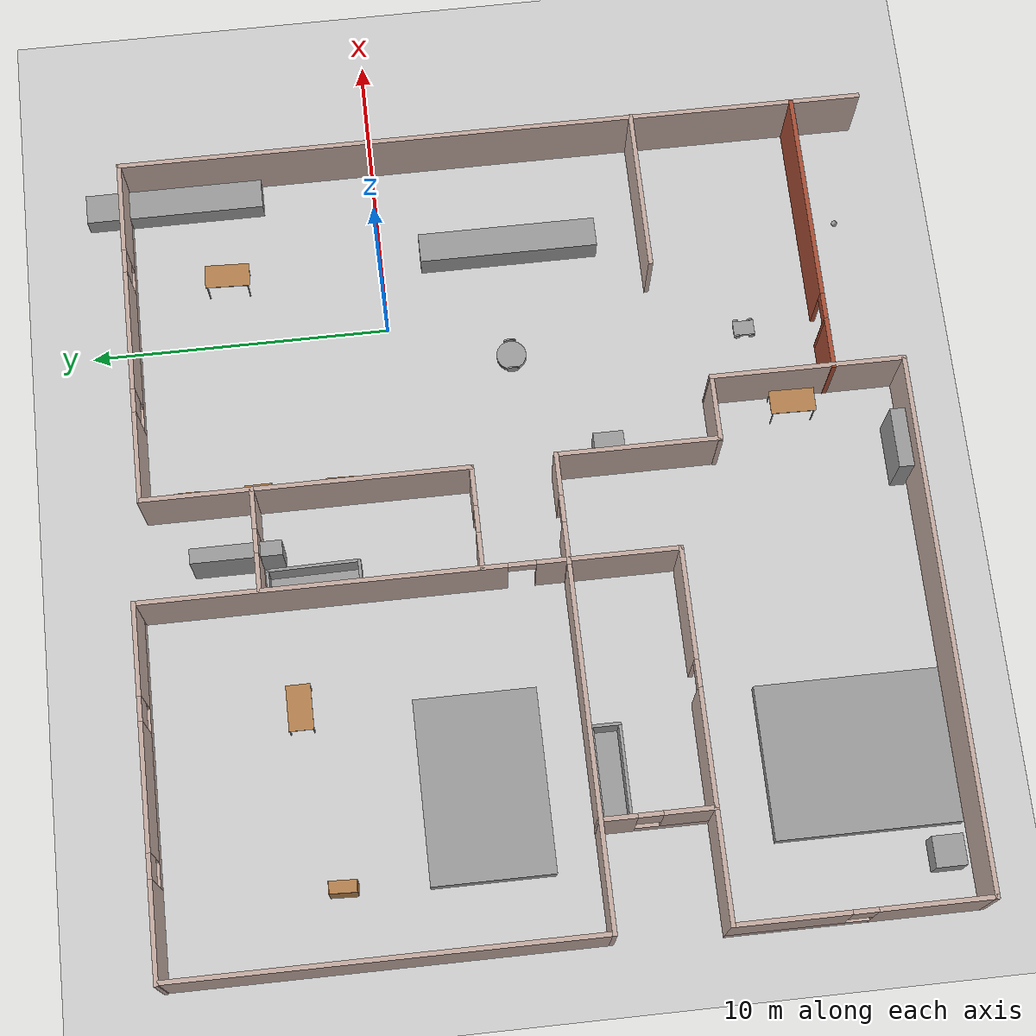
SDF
<sdf version="1.6">
 <world name="default">
  <plugin name="hello" filename="libhello.so"/>
  <light name="sun" type="directional">
   <pose>0 0 10 0 -0 0</pose>
   <diffuse>0.8 0.8 0.8 1</diffuse>
   <specular>0.2 0.2 0.2 1</specular>
   <attenuation>
    <range>1000</range>
    <constant>0.9</constant>
    <linear>0.01</linear>
    <quadratic>0.001</quadratic>
   </attenuation>
   <direction>-0.5 0.1 -0.9</direction>
  </light>
  <model name="ground_plane">
   <static>1</static>
   <link name="link">
    <collision name="collision">
     <geometry><plane><normal>0 0 1</normal><size>100 100</size></plane></geometry>
     <surface>
      <contact><collide_bitmask>65535</collide_bitmask></contact>
      <friction><ode><mu>100</mu><mu2>50</mu2></ode></friction>
     </surface>
    </collision>
    <visual name="visual">
     <cast_shadows>0</cast_shadows>
     <geometry><plane><normal>0 0 1</normal><size>100 100</size></plane></geometry>
     <material>
      <script><uri>file://media/materials/scripts/gazebo.material</uri><name>Gazebo/Grey</name></script>
     </material>
    </visual>
   </link>
  </model>
  <gravity>0 0 -9.8</gravity>
  <magnetic_field>6e-06 2.3e-05 -4.2e-05</magnetic_field>
  <atmosphere type="adiabatic"/>
  <physics name="default_physics" default="0" type="ode">
   <max_step_size>0.001</max_step_size>
   <real_time_factor>1</real_time_factor>
   <real_time_update_rate>1000</real_time_update_rate>
  </physics>
  <scene><ambient>0.4 0.4 0.4 1</ambient><background>0.7 0.7 0.7 1</background><shadows>1</shadows></scene>
  <spherical_coordinates>
   <surface_model>EARTH_WGS84</surface_model>
   <latitude_deg>0</latitude_deg>
   <longitude_deg>0</longitude_deg>
   <elevation>0</elevation>
   <heading_deg>0</heading_deg>
  </spherical_coordinates>
  <model name="ksl_room">
   <pose>-7.675 -3.93877 0 0 -0 0</pose>
   <link name="Wall_17">
    <collision name="Wall_17_Collision">
     <geometry><box><size>14 0.15 2.5</size></box></geometry>
     <pose>0 0 1.25 0 -0 0</pose>
    </collision>
    <visual name="Wall_17_Visual">
     <pose>0 0 1.25 0 -0 0</pose>
     <geometry><box><size>14 0.15 2.5</size></box></geometry>
     <material>
      <script><uri>file://media/materials/scripts/gazebo.material</uri><name>Gazebo/Grey</name></script>
      <ambient>0.760784 0.662745 0.627451 1</ambient>
     </material>
     <meta><layer>0</layer></meta>
    </visual>
    <pose>-13.4754 5.836 0 0 0 -1.5708</pose>
   </link>
   <link name="Wall_18">
    <collision name="Wall_18_Collision">
     <geometry><box><size>11.9733 0.15 2.5</size></box></geometry>
     <pose>0 0 1.25 0 -0 0</pose>
    </collision>
    <visual name="Wall_18_Visual">
     <pose>0 0 1.25 0 -0 0</pose>
     <geometry><box><size>11.9733 0.15 2.5</size></box></geometry>
     <material>
      <script><uri>file://media/materials/scripts/gazebo.material</uri><name>Gazebo/Grey</name></script>
      <ambient>0.760784 0.662745 0.627451 1</ambient>
     </material>
     <meta><layer>0</layer></meta>
    </visual>
    <pose>-7.56394 -1.082 0 0 -0 0.001184</pose>
   </link>
   <link name="Wall_22">
    <pose>-7.57744 12.775 0 0 -0 0</pose>
    <visual name="Wall_22_Visual_0">
     <pose>-4.38866 0 1.25 0 -0 0</pose>
     <geometry><box><size>3.22267 0.15 2.5</size></box></geometry>
     <material>
      <script><uri>file://media/materials/scripts/gazebo.material</uri><name>Gazebo/Grey</name></script>
      <ambient>0.760784 0.662745 0.627451 1</ambient>
     </material>
     <meta><layer>0</layer></meta>
    </visual>
    <collision name="Wall_22_Collision_0">
     <geometry><box><size>3.22267 0.15 2.5</size></box></geometry>
     <pose>-4.38866 0 1.25 0 -0 0</pose>
    </collision>
    <visual name="Wall_22_Visual_1">
     <pose>1.61133 0 0.25 0 -0 0</pose>
     <geometry><box><size>8.77733 0.15 0.5</size></box></geometry>
     <material>
      <script><uri>file://media/materials/scripts/gazebo.material</uri><name>Gazebo/Grey</name></script>
      <ambient>0.760784 0.662745 0.627451 1</ambient>
     </material>
     <meta><layer>0</layer></meta>
    </visual>
    <collision name="Wall_22_Collision_1">
     <geometry><box><size>8.77733 0.15 0.5</size></box></geometry>
     <pose>1.61133 0 0.25 0 -0 0</pose>
    </collision>
    <visual name="Wall_22_Visual_2">
     <pose>0.07765 0 1.5 0 -0 0</pose>
     <geometry><box><size>4.10996 0.15 2</size></box></geometry>
     <material>
      <script><uri>file://media/materials/scripts/gazebo.material</uri><name>Gazebo/Grey</name></script>
      <ambient>0.760784 0.662745 0.627451 1</ambient>
     </material>
     <meta><layer>0</layer></meta>
    </visual>
    <collision name="Wall_22_Collision_2">
     <geometry><box><size>4.10996 0.15 2</size></box></geometry>
     <pose>0.07765 0 1.5 0 -0 0</pose>
    </collision>
    <visual name="Wall_22_Visual_3">
     <pose>4.46631 0 1.5 0 -0 0</pose>
     <geometry><box><size>3.06737 0.15 2</size></box></geometry>
     <material>
      <script><uri>file://media/materials/scripts/gazebo.material</uri><name>Gazebo/Grey</name></script>
      <ambient>0.760784 0.662745 0.627451 1</ambient>
     </material>
     <meta><layer>0</layer></meta>
    </visual>
    <collision name="Wall_22_Collision_3">
     <geometry><box><size>3.06737 0.15 2</size></box></geometry>
     <pose>4.46631 0 1.5 0 -0 0</pose>
    </collision>
    <visual name="Wall_22_Visual_4">
     <pose>-2.37733 0 1.9 0 -0 0</pose>
     <geometry><box><size>0.8 0.15 1.2</size></box></geometry>
     <material>
      <script><uri>file://media/materials/scripts/gazebo.material</uri><name>Gazebo/Grey</name></script>
      <ambient>0.760784 0.662745 0.627451 1</ambient>
     </material>
     <meta><layer>0</layer></meta>
    </visual>
    <collision name="Wall_22_Collision_4">
     <geometry><box><size>0.8 0.15 1.2</size></box></geometry>
     <pose>-2.37733 0 1.9 0 -0 0</pose>
    </collision>
    <visual name="Wall_22_Visual_5">
     <pose>2.53263 0 1.9 0 -0 0</pose>
     <geometry><box><size>0.8 0.15 1.2</size></box></geometry>
     <material>
      <script><uri>file://media/materials/scripts/gazebo.material</uri><name>Gazebo/Grey</name></script>
      <ambient>0.760784 0.662745 0.627451 1</ambient>
     </material>
     <meta><layer>0</layer></meta>
    </visual>
    <collision name="Wall_22_Collision_5">
     <geometry><box><size>0.8 0.15 1.2</size></box></geometry>
     <pose>2.53263 0 1.9 0 -0 0</pose>
    </collision>
   </link>
   <link name="Wall_23">
    <pose>-1.65244 5.85 0 0 0 -1.5708</pose>
    <visual name="Wall_23_Visual_0">
     <pose>-1.00938 0 1.25 0 -0 0</pose>
     <geometry><box><size>11.9812 0.15 2.5</size></box></geometry>
     <material>
      <script><uri>file://media/materials/scripts/gazebo.material</uri><name>Gazebo/Grey</name></script>
      <ambient>0.760784 0.662745 0.627451 1</ambient>
     </material>
     <meta><layer>0</layer></meta>
    </visual>
    <collision name="Wall_23_Collision_0">
     <geometry><box><size>11.9812 0.15 2.5</size></box></geometry>
     <pose>-1.00938 0 1.25 0 -0 0</pose>
    </collision>
    <visual name="Wall_23_Visual_1">
     <pose>6.44062 0 1.25 0 -0 0</pose>
     <geometry><box><size>1.11876 0.15 2.5</size></box></geometry>
     <material>
      <script><uri>file://media/materials/scripts/gazebo.material</uri><name>Gazebo/Grey</name></script>
      <ambient>0.760784 0.662745 0.627451 1</ambient>
     </material>
     <meta><layer>0</layer></meta>
    </visual>
    <collision name="Wall_23_Collision_1">
     <geometry><box><size>1.11876 0.15 2.5</size></box></geometry>
     <pose>6.44062 0 1.25 0 -0 0</pose>
    </collision>
    <visual name="Wall_23_Visual_2">
     <pose>5.43124 0 2.25 0 -0 0</pose>
     <geometry><box><size>0.9 0.15 0.5</size></box></geometry>
     <material>
      <script><uri>file://media/materials/scripts/gazebo.material</uri><name>Gazebo/Grey</name></script>
      <ambient>0.760784 0.662745 0.627451 1</ambient>
     </material>
     <meta><layer>0</layer></meta>
    </visual>
    <collision name="Wall_23_Collision_2">
     <geometry><box><size>0.9 0.15 0.5</size></box></geometry>
     <pose>5.43124 0 2.25 0 -0 0</pose>
    </collision>
   </link>
   <link name="Wall_25">
    <pose>-10.0024 -2.875 0 0 0 -1.5708</pose>
    <visual name="Wall_25_Visual_0">
     <pose>-1.25876 0 1.25 0 -0 0</pose>
     <geometry><box><size>1.23249 0.15 2.5</size></box></geometry>
     <material>
      <script><uri>file://media/materials/scripts/gazebo.material</uri><name>Gazebo/Grey</name></script>
      <ambient>0.760784 0.662745 0.627451 1</ambient>
     </material>
     <meta><layer>0</layer></meta>
    </visual>
    <collision name="Wall_25_Collision_0">
     <geometry><box><size>1.23249 0.15 2.5</size></box></geometry>
     <pose>-1.25876 0 1.25 0 -0 0</pose>
    </collision>
    <visual name="Wall_25_Visual_1">
     <pose>0.616244 0 0.25 0 -0 0</pose>
     <geometry><box><size>2.51751 0.15 0.5</size></box></geometry>
     <material>
      <script><uri>file://media/materials/scripts/gazebo.material</uri><name>Gazebo/Grey</name></script>
      <ambient>0.760784 0.662745 0.627451 1</ambient>
     </material>
     <meta><layer>0</layer></meta>
    </visual>
    <collision name="Wall_25_Collision_1">
     <geometry><box><size>2.51751 0.15 0.5</size></box></geometry>
     <pose>0.616244 0 0.25 0 -0 0</pose>
    </collision>
    <visual name="Wall_25_Visual_2">
     <pose>1.01624 0 1.5 0 -0 0</pose>
     <geometry><box><size>1.71751 0.15 2</size></box></geometry>
     <material>
      <script><uri>file://media/materials/scripts/gazebo.material</uri><name>Gazebo/Grey</name></script>
      <ambient>0.760784 0.662745 0.627451 1</ambient>
     </material>
     <meta><layer>0</layer></meta>
    </visual>
    <collision name="Wall_25_Collision_2">
     <geometry><box><size>1.71751 0.15 2</size></box></geometry>
     <pose>1.01624 0 1.5 0 -0 0</pose>
    </collision>
    <visual name="Wall_25_Visual_3">
     <pose>-0.242512 0 1.9 0 -0 0</pose>
     <geometry><box><size>0.8 0.15 1.2</size></box></geometry>
     <material>
      <script><uri>file://media/materials/scripts/gazebo.material</uri><name>Gazebo/Grey</name></script>
      <ambient>0.760784 0.662745 0.627451 1</ambient>
     </material>
     <meta><layer>0</layer></meta>
    </visual>
    <collision name="Wall_25_Collision_3">
     <geometry><box><size>0.8 0.15 1.2</size></box></geometry>
     <pose>-0.242512 0 1.9 0 -0 0</pose>
    </collision>
   </link>
   <link name="Wall_26">
    <pose>-5.82744 -4.675 0 0 -0 0</pose>
    <visual name="Wall_26_Visual_0">
     <pose>-2.3202 0 1.25 0 -0 0</pose>
     <geometry><box><size>3.85961 0.15 2.5</size></box></geometry>
     <material>
      <script><uri>file://media/materials/scripts/gazebo.material</uri><name>Gazebo/Grey</name></script>
      <ambient>0.760784 0.662745 0.627451 1</ambient>
     </material>
     <meta><layer>0</layer></meta>
    </visual>
    <collision name="Wall_26_Collision_0">
     <geometry><box><size>3.85961 0.15 2.5</size></box></geometry>
     <pose>-2.3202 0 1.25 0 -0 0</pose>
    </collision>
    <visual name="Wall_26_Visual_1">
     <pose>2.3798 0 1.25 0 -0 0</pose>
     <geometry><box><size>3.74039 0.15 2.5</size></box></geometry>
     <material>
      <script><uri>file://media/materials/scripts/gazebo.material</uri><name>Gazebo/Grey</name></script>
      <ambient>0.760784 0.662745 0.627451 1</ambient>
     </material>
     <meta><layer>0</layer></meta>
    </visual>
    <collision name="Wall_26_Collision_1">
     <geometry><box><size>3.74039 0.15 2.5</size></box></geometry>
     <pose>2.3798 0 1.25 0 -0 0</pose>
    </collision>
    <visual name="Wall_26_Visual_2">
     <pose>0.059605 0 2.25 0 -0 0</pose>
     <geometry><box><size>0.9 0.15 0.5</size></box></geometry>
     <material>
      <script><uri>file://media/materials/scripts/gazebo.material</uri><name>Gazebo/Grey</name></script>
      <ambient>0.760784 0.662745 0.627451 1</ambient>
     </material>
     <meta><layer>0</layer></meta>
    </visual>
    <collision name="Wall_26_Collision_2">
     <geometry><box><size>0.9 0.15 0.5</size></box></geometry>
     <pose>0.059605 0 2.25 0 -0 0</pose>
    </collision>
   </link>
   <link name="Wall_27">
    <collision name="Wall_27_Collision">
     <geometry><box><size>3.75 0.15 2.5</size></box></geometry>
     <pose>0 0 1.25 0 -0 0</pose>
    </collision>
    <visual name="Wall_27_Visual">
     <pose>0 0 1.25 0 -0 0</pose>
     <geometry><box><size>3.75 0.15 2.5</size></box></geometry>
     <material>
      <script><uri>file://media/materials/scripts/gazebo.material</uri><name>Gazebo/Grey</name></script>
      <ambient>0.760784 0.662745 0.627451 1</ambient>
     </material>
     <meta><layer>0</layer></meta>
    </visual>
    <pose>-1.65244 -2.875 0 0 -0 1.5708</pose>
   </link>
   <link name="Wall_31">
    <pose>0.067219 -1.075 0 0 -0 0</pose>
    <visual name="Wall_31_Visual_0">
     <pose>-1.17954 0 1.25 0 -0 0</pose>
     <geometry><box><size>1.41114 0.15 2.5</size></box></geometry>
     <material>
      <script><uri>file://media/materials/scripts/gazebo.material</uri><name>Gazebo/Grey</name></script>
      <ambient>0.760784 0.662745 0.627451 1</ambient>
     </material>
     <meta><layer>0</layer></meta>
    </visual>
    <collision name="Wall_31_Collision_0">
     <geometry><box><size>1.41114 0.15 2.5</size></box></geometry>
     <pose>-1.17954 0 1.25 0 -0 0</pose>
    </collision>
    <visual name="Wall_31_Visual_1">
     <pose>1.15557 0 1.25 0 -0 0</pose>
     <geometry><box><size>1.45908 0.15 2.5</size></box></geometry>
     <material>
      <script><uri>file://media/materials/scripts/gazebo.material</uri><name>Gazebo/Grey</name></script>
      <ambient>0.760784 0.662745 0.627451 1</ambient>
     </material>
     <meta><layer>0</layer></meta>
    </visual>
    <collision name="Wall_31_Collision_1">
     <geometry><box><size>1.45908 0.15 2.5</size></box></geometry>
     <pose>1.15557 0 1.25 0 -0 0</pose>
    </collision>
    <visual name="Wall_31_Visual_2">
     <pose>-0.023972 0 2.25 0 -0 0</pose>
     <geometry><box><size>0.9 0.15 0.5</size></box></geometry>
     <material>
      <script><uri>file://media/materials/scripts/gazebo.material</uri><name>Gazebo/Grey</name></script>
      <ambient>0.760784 0.662745 0.627451 1</ambient>
     </material>
     <meta><layer>0</layer></meta>
    </visual>
    <collision name="Wall_31_Collision_2">
     <geometry><box><size>0.9 0.15 0.5</size></box></geometry>
     <pose>-0.023972 0 2.25 0 -0 0</pose>
    </collision>
   </link>
   <link name="Wall_32">
    <collision name="Wall_32_Collision">
     <geometry><box><size>5.5 0.15 2.5</size></box></geometry>
     <pose>0 0 1.25 0 -0 0</pose>
    </collision>
    <visual name="Wall_32_Visual">
     <pose>0 0 1.25 0 -0 0</pose>
     <geometry><box><size>5.5 0.15 2.5</size></box></geometry>
     <material>
      <script><uri>file://media/materials/scripts/gazebo.material</uri><name>Gazebo/Grey</name></script>
      <ambient>0.760784 0.662745 0.627451 1</ambient>
     </material>
     <meta><layer>0</layer></meta>
    </visual>
    <pose>1.87733 -3.75 0 0 0 -1.5708</pose>
   </link>
   <link name="Wall_33">
    <collision name="Wall_33_Collision">
     <geometry><box><size>2.29046 0.15 2.5</size></box></geometry>
     <pose>0 0 1.25 0 -0 0</pose>
    </collision>
    <visual name="Wall_33_Visual">
     <pose>0 0 1.25 0 -0 0</pose>
     <geometry><box><size>2.29046 0.15 2.5</size></box></geometry>
     <material>
      <script><uri>file://media/materials/scripts/gazebo.material</uri><name>Gazebo/Grey</name></script>
      <ambient>0.760784 0.662745 0.627451 1</ambient>
     </material>
     <meta><layer>0</layer></meta>
    </visual>
    <pose>2.92733 -6.425 0 0 -0 0</pose>
   </link>
   <link name="Wall_34">
    <collision name="Wall_34_Collision">
     <geometry><box><size>6.5 0.15 2.5</size></box></geometry>
     <pose>0 0 1.25 0 -0 0</pose>
    </collision>
    <visual name="Wall_34_Visual">
     <pose>0 0 1.25 0 -0 0</pose>
     <geometry><box><size>6.5 0.15 2.5</size></box></geometry>
     <material>
      <script><uri>file://media/materials/scripts/gazebo.material</uri><name>Gazebo/Grey</name></script>
      <ambient>0.760784 0.662745 0.627451 1</ambient>
     </material>
     <meta><layer>0</layer></meta>
    </visual>
    <pose>3.99756 -9.6 0 0 0 -1.5708</pose>
   </link>
   <link name="Wall_35">
    <collision name="Wall_35_Collision">
     <geometry><box><size>17.75 0.15 2.5</size></box></geometry>
     <pose>0 0 1.25 0 -0 0</pose>
    </collision>
    <visual name="Wall_35_Visual">
     <pose>0 0 1.25 0 -0 0</pose>
     <geometry><box><size>17.75 0.15 2.5</size></box></geometry>
     <material>
      <script><uri>file://media/materials/scripts/gazebo.material</uri><name>Gazebo/Grey</name></script>
      <ambient>0.760784 0.662745 0.627451 1</ambient>
     </material>
     <meta><layer>0</layer></meta>
    </visual>
    <pose>-4.80244 -12.775 0 0 -0 3.14159</pose>
   </link>
   <link name="Wall_36">
    <pose>-13.6024 -8.725 0 0 -0 1.5708</pose>
    <visual name="Wall_36_Visual_0">
     <pose>-2.27357 0 1.25 0 -0 0</pose>
     <geometry><box><size>3.70287 0.15 2.5</size></box></geometry>
     <material>
      <script><uri>file://media/materials/scripts/gazebo.material</uri><name>Gazebo/Grey</name></script>
      <ambient>0.760784 0.662745 0.627451 1</ambient>
     </material>
     <meta><layer>0</layer></meta>
    </visual>
    <collision name="Wall_36_Collision_0">
     <geometry><box><size>3.70287 0.15 2.5</size></box></geometry>
     <pose>-2.27357 0 1.25 0 -0 0</pose>
    </collision>
    <visual name="Wall_36_Visual_1">
     <pose>1.85143 0 0.25 0 -0 0</pose>
     <geometry><box><size>4.54713 0.15 0.5</size></box></geometry>
     <material>
      <script><uri>file://media/materials/scripts/gazebo.material</uri><name>Gazebo/Grey</name></script>
      <ambient>0.760784 0.662745 0.627451 1</ambient>
     </material>
     <meta><layer>0</layer></meta>
    </visual>
    <collision name="Wall_36_Collision_1">
     <geometry><box><size>4.54713 0.15 0.5</size></box></geometry>
     <pose>1.85143 0 0.25 0 -0 0</pose>
    </collision>
    <visual name="Wall_36_Visual_2">
     <pose>2.25143 0 1.5 0 -0 0</pose>
     <geometry><box><size>3.74713 0.15 2</size></box></geometry>
     <material>
      <script><uri>file://media/materials/scripts/gazebo.material</uri><name>Gazebo/Grey</name></script>
      <ambient>0.760784 0.662745 0.627451 1</ambient>
     </material>
     <meta><layer>0</layer></meta>
    </visual>
    <collision name="Wall_36_Collision_2">
     <geometry><box><size>3.74713 0.15 2</size></box></geometry>
     <pose>2.25143 0 1.5 0 -0 0</pose>
    </collision>
    <visual name="Wall_36_Visual_3">
     <pose>-0.022129 0 1.9 0 -0 0</pose>
     <geometry><box><size>0.8 0.15 1.2</size></box></geometry>
     <material>
      <script><uri>file://media/materials/scripts/gazebo.material</uri><name>Gazebo/Grey</name></script>
      <ambient>0.760784 0.662745 0.627451 1</ambient>
     </material>
     <meta><layer>0</layer></meta>
    </visual>
    <collision name="Wall_36_Collision_3">
     <geometry><box><size>0.8 0.15 1.2</size></box></geometry>
     <pose>-0.022129 0 1.9 0 -0 0</pose>
    </collision>
   </link>
   <link name="Wall_37">
    <collision name="Wall_37_Collision">
     <geometry><box><size>3.75 0.15 2.5</size></box></geometry>
     <pose>0 0 1.25 0 -0 0</pose>
    </collision>
    <visual name="Wall_37_Visual">
     <pose>0 0 1.25 0 -0 0</pose>
     <geometry><box><size>3.75 0.15 2.5</size></box></geometry>
     <material>
      <script><uri>file://media/materials/scripts/gazebo.material</uri><name>Gazebo/Grey</name></script>
      <ambient>0.760784 0.662745 0.627451 1</ambient>
     </material>
     <meta><layer>0</layer></meta>
    </visual>
    <pose>-11.8024 -4.675 0 0 -0 0</pose>
   </link>
   <link name="Wall_41">
    <pose>0.063923 1.68558 0 0 -0 0</pose>
    <visual name="Wall_41_Visual_0">
     <pose>-1.13698 0 1.25 0 -0 0</pose>
     <geometry><box><size>1.22605 0.15 2.5</size></box></geometry>
     <material>
      <script><uri>file://media/materials/scripts/gazebo.material</uri><name>Gazebo/Grey</name></script>
      <ambient>0.760784 0.662745 0.627451 1</ambient>
     </material>
     <meta><layer>0</layer></meta>
    </visual>
    <collision name="Wall_41_Collision_0">
     <geometry><box><size>1.22605 0.15 2.5</size></box></geometry>
     <pose>-1.13698 0 1.25 0 -0 0</pose>
    </collision>
    <visual name="Wall_41_Visual_1">
     <pose>1.06303 0 1.25 0 -0 0</pose>
     <geometry><box><size>1.37395 0.15 2.5</size></box></geometry>
     <material>
      <script><uri>file://media/materials/scripts/gazebo.material</uri><name>Gazebo/Grey</name></script>
      <ambient>0.760784 0.662745 0.627451 1</ambient>
     </material>
     <meta><layer>0</layer></meta>
    </visual>
    <collision name="Wall_41_Collision_1">
     <geometry><box><size>1.37395 0.15 2.5</size></box></geometry>
     <pose>1.06303 0 1.25 0 -0 0</pose>
    </collision>
    <visual name="Wall_41_Visual_2">
     <pose>-0.073951 0 2.25 0 -0 0</pose>
     <geometry><box><size>0.9 0.15 0.5</size></box></geometry>
     <material>
      <script><uri>file://media/materials/scripts/gazebo.material</uri><name>Gazebo/Grey</name></script>
      <ambient>0.760784 0.662745 0.627451 1</ambient>
     </material>
     <meta><layer>0</layer></meta>
    </visual>
    <collision name="Wall_41_Collision_2">
     <geometry><box><size>0.9 0.15 0.5</size></box></geometry>
     <pose>-0.073951 0 2.25 0 -0 0</pose>
    </collision>
   </link>
   <link name="Wall_42">
    <collision name="Wall_42_Collision">
     <geometry><box><size>7.25 0.15 2.5</size></box></geometry>
     <pose>0 0 1.25 0 -0 0</pose>
    </collision>
    <visual name="Wall_42_Visual">
     <pose>0 0 1.25 0 -0 0</pose>
     <geometry><box><size>7.25 0.15 2.5</size></box></geometry>
     <material>
      <script><uri>file://media/materials/scripts/gazebo.material</uri><name>Gazebo/Grey</name></script>
      <ambient>0.760784 0.662745 0.627451 1</ambient>
     </material>
     <meta><layer>0</layer></meta>
    </visual>
    <pose>1.73892 5.23558 0 0 -0 1.5708</pose>
   </link>
   <link name="Wall_43">
    <pose>0.063923 8.78558 0 0 -0 3.14159</pose>
    <visual name="Wall_43_Visual_0">
     <pose>-1.04439 0 1.25 0 -0 0</pose>
     <geometry><box><size>1.41121 0.15 2.5</size></box></geometry>
     <material>
      <script><uri>file://media/materials/scripts/gazebo.material</uri><name>Gazebo/Grey</name></script>
      <ambient>0.760784 0.662745 0.627451 1</ambient>
     </material>
     <meta><layer>0</layer></meta>
    </visual>
    <collision name="Wall_43_Collision_0">
     <geometry><box><size>1.41121 0.15 2.5</size></box></geometry>
     <pose>-1.04439 0 1.25 0 -0 0</pose>
    </collision>
    <visual name="Wall_43_Visual_1">
     <pose>0.705606 0 0.25 0 -0 0</pose>
     <geometry><box><size>2.08879 0.15 0.5</size></box></geometry>
     <material>
      <script><uri>file://media/materials/scripts/gazebo.material</uri><name>Gazebo/Grey</name></script>
      <ambient>0.760784 0.662745 0.627451 1</ambient>
     </material>
     <meta><layer>0</layer></meta>
    </visual>
    <collision name="Wall_43_Collision_1">
     <geometry><box><size>2.08879 0.15 0.5</size></box></geometry>
     <pose>0.705606 0 0.25 0 -0 0</pose>
    </collision>
    <visual name="Wall_43_Visual_2">
     <pose>1.10561 0 1.5 0 -0 0</pose>
     <geometry><box><size>1.28879 0.15 2</size></box></geometry>
     <material>
      <script><uri>file://media/materials/scripts/gazebo.material</uri><name>Gazebo/Grey</name></script>
      <ambient>0.760784 0.662745 0.627451 1</ambient>
     </material>
     <meta><layer>0</layer></meta>
    </visual>
    <collision name="Wall_43_Collision_2">
     <geometry><box><size>1.28879 0.15 2</size></box></geometry>
     <pose>1.10561 0 1.5 0 -0 0</pose>
    </collision>
    <visual name="Wall_43_Visual_3">
     <pose>0.061212 0 1.9 0 -0 0</pose>
     <geometry><box><size>0.8 0.15 1.2</size></box></geometry>
     <material>
      <script><uri>file://media/materials/scripts/gazebo.material</uri><name>Gazebo/Grey</name></script>
      <ambient>0.760784 0.662745 0.627451 1</ambient>
     </material>
     <meta><layer>0</layer></meta>
    </visual>
    <collision name="Wall_43_Collision_3">
     <geometry><box><size>0.8 0.15 1.2</size></box></geometry>
     <pose>0.061212 0 1.9 0 -0 0</pose>
    </collision>
   </link>
   <link name="Wall_45">
    <collision name="Wall_45_Collision">
     <geometry><box><size>3.75 0.15 2.5</size></box></geometry>
     <pose>0 0 1.25 0 -0 0</pose>
    </collision>
    <visual name="Wall_45_Visual">
     <pose>0 0 1.25 0 -0 0</pose>
     <geometry><box><size>3.75 0.15 2.5</size></box></geometry>
     <material>
      <script><uri>file://media/materials/scripts/gazebo.material</uri><name>Gazebo/Grey</name></script>
      <ambient>0.760784 0.662745 0.627451 1</ambient>
     </material>
     <meta><layer>0</layer></meta>
    </visual>
    <pose>1.73892 10.5856 0 0 -0 1.5708</pose>
   </link>
   <link name="Wall_46">
    <pose>7.66392 12.3856 0 0 -0 0</pose>
    <visual name="Wall_46_Visual_0">
     <pose>-4.44872 0 1.25 0 -0 0</pose>
     <geometry><box><size>3.10256 0.15 2.5</size></box></geometry>
     <material>
      <script><uri>file://media/materials/scripts/gazebo.material</uri><name>Gazebo/Grey</name></script>
      <ambient>0.760784 0.662745 0.627451 1</ambient>
     </material>
     <meta><layer>0</layer></meta>
    </visual>
    <collision name="Wall_46_Collision_0">
     <geometry><box><size>3.10256 0.15 2.5</size></box></geometry>
     <pose>-4.44872 0 1.25 0 -0 0</pose>
    </collision>
    <visual name="Wall_46_Visual_1">
     <pose>1.55128 0 0.25 0 -0 0</pose>
     <geometry><box><size>8.89744 0.15 0.5</size></box></geometry>
     <material>
      <script><uri>file://media/materials/scripts/gazebo.material</uri><name>Gazebo/Grey</name></script>
      <ambient>0.760784 0.662745 0.627451 1</ambient>
     </material>
     <meta><layer>0</layer></meta>
    </visual>
    <collision name="Wall_46_Collision_1">
     <geometry><box><size>8.89744 0.15 0.5</size></box></geometry>
     <pose>1.55128 0 0.25 0 -0 0</pose>
    </collision>
    <visual name="Wall_46_Visual_2">
     <pose>-0.024665 0 1.5 0 -0 0</pose>
     <geometry><box><size>4.14554 0.15 2</size></box></geometry>
     <material>
      <script><uri>file://media/materials/scripts/gazebo.material</uri><name>Gazebo/Grey</name></script>
      <ambient>0.760784 0.662745 0.627451 1</ambient>
     </material>
     <meta><layer>0</layer></meta>
    </visual>
    <collision name="Wall_46_Collision_2">
     <geometry><box><size>4.14554 0.15 2</size></box></geometry>
     <pose>-0.024665 0 1.5 0 -0 0</pose>
    </collision>
    <visual name="Wall_46_Visual_3">
     <pose>4.42405 0 1.5 0 -0 0</pose>
     <geometry><box><size>3.1519 0.15 2</size></box></geometry>
     <material>
      <script><uri>file://media/materials/scripts/gazebo.material</uri><name>Gazebo/Grey</name></script>
      <ambient>0.760784 0.662745 0.627451 1</ambient>
     </material>
     <meta><layer>0</layer></meta>
    </visual>
    <collision name="Wall_46_Collision_3">
     <geometry><box><size>3.1519 0.15 2</size></box></geometry>
     <pose>4.42405 0 1.5 0 -0 0</pose>
    </collision>
    <visual name="Wall_46_Visual_4">
     <pose>-2.49744 0 1.9 0 -0 0</pose>
     <geometry><box><size>0.8 0.15 1.2</size></box></geometry>
     <material>
      <script><uri>file://media/materials/scripts/gazebo.material</uri><name>Gazebo/Grey</name></script>
      <ambient>0.760784 0.662745 0.627451 1</ambient>
     </material>
     <meta><layer>0</layer></meta>
    </visual>
    <collision name="Wall_46_Collision_4">
     <geometry><box><size>0.8 0.15 1.2</size></box></geometry>
     <pose>-2.49744 0 1.9 0 -0 0</pose>
    </collision>
    <visual name="Wall_46_Visual_5">
     <pose>2.4481 0 1.9 0 -0 0</pose>
     <geometry><box><size>0.8 0.15 1.2</size></box></geometry>
     <material>
      <script><uri>file://media/materials/scripts/gazebo.material</uri><name>Gazebo/Grey</name></script>
      <ambient>0.760784 0.662745 0.627451 1</ambient>
     </material>
     <meta><layer>0</layer></meta>
    </visual>
    <collision name="Wall_46_Collision_5">
     <geometry><box><size>0.8 0.15 1.2</size></box></geometry>
     <pose>2.4481 0 1.9 0 -0 0</pose>
    </collision>
   </link>
   <link name="Wall_47">
    <collision name="Wall_47_Collision">
     <geometry><box><size>25.25 0.15 2.5</size></box></geometry>
     <pose>0 0 1.25 0 -0 0</pose>
    </collision>
    <visual name="Wall_47_Visual">
     <pose>0 0 1.25 0 -0 0</pose>
     <geometry><box><size>25.25 0.15 2.5</size></box></geometry>
     <material>
      <script><uri>file://media/materials/scripts/gazebo.material</uri><name>Gazebo/Grey</name></script>
      <ambient>0.760784 0.662745 0.627451 1</ambient>
     </material>
     <meta><layer>0</layer></meta>
    </visual>
    <pose>13.5889 -0.164423 0 0 0 -1.5708</pose>
   </link>
   <link name="Wall_49">
    <collision name="Wall_49_Collision">
     <geometry><box><size>1.75 0.15 2.5</size></box></geometry>
     <pose>0 0 1.25 0 -0 0</pose>
    </collision>
    <visual name="Wall_49_Visual">
     <pose>0 0 1.25 0 -0 0</pose>
     <geometry><box><size>1.75 0.15 2.5</size></box></geometry>
     <material>
      <script><uri>file://media/materials/scripts/gazebo.material</uri><name>Gazebo/Bricks</name></script>
      <ambient>1 1 1 1</ambient>
     </material>
     <meta><layer>0</layer></meta>
    </visual>
    <pose>4.77111 -10.4501 0 0 -0 0</pose>
   </link>
   <link name="Wall_51">
    <pose>9.55987 -10.4501 0 0 -0 3.14159</pose>
    <visual name="Wall_51_Visual_0">
     <pose>-0.511723 0 1.25 0 -0 0</pose>
     <geometry><box><size>7.10408 0.15 2.5</size></box></geometry>
     <material>
      <script><uri>file://media/materials/scripts/gazebo.material</uri><name>Gazebo/Bricks</name></script>
      <ambient>1 1 1 1</ambient>
     </material>
     <meta><layer>0</layer></meta>
    </visual>
    <collision name="Wall_51_Collision_0">
     <geometry><box><size>7.10408 0.15 2.5</size></box></geometry>
     <pose>-0.511723 0 1.25 0 -0 0</pose>
    </collision>
    <visual name="Wall_51_Visual_1">
     <pose>4.00204 0 1.25 0 -0 0</pose>
     <geometry><box><size>0.123447 0.15 2.5</size></box></geometry>
     <material>
      <script><uri>file://media/materials/scripts/gazebo.material</uri><name>Gazebo/Bricks</name></script>
      <ambient>1 1 1 1</ambient>
     </material>
     <meta><layer>0</layer></meta>
    </visual>
    <collision name="Wall_51_Collision_1">
     <geometry><box><size>0.123447 0.15 2.5</size></box></geometry>
     <pose>4.00204 0 1.25 0 -0 0</pose>
    </collision>
    <visual name="Wall_51_Visual_2">
     <pose>3.49032 0 2.25 0 -0 0</pose>
     <geometry><box><size>0.9 0.15 0.5</size></box></geometry>
     <material>
      <script><uri>file://media/materials/scripts/gazebo.material</uri><name>Gazebo/Bricks</name></script>
      <ambient>1 1 1 1</ambient>
     </material>
     <meta><layer>0</layer></meta>
    </visual>
    <collision name="Wall_51_Collision_2">
     <geometry><box><size>0.9 0.15 0.5</size></box></geometry>
     <pose>3.49032 0 2.25 0 -0 0</pose>
    </collision>
   </link>
   <link name="Wall_53">
    <collision name="Wall_53_Collision">
     <geometry><box><size>5.5 0.15 2.5</size></box></geometry>
     <pose>0 0 1.25 0 -0 0</pose>
    </collision>
    <visual name="Wall_53_Visual">
     <pose>0 0 1.25 0 -0 0</pose>
     <geometry><box><size>5.5 0.15 2.5</size></box></geometry>
     <material>
      <script><uri>file://media/materials/scripts/gazebo.material</uri><name>Gazebo/Grey</name></script>
      <ambient>0.760784 0.662745 0.627451 1</ambient>
     </material>
     <meta><layer>0</layer></meta>
    </visual>
    <pose>10.9274 -4.96187 0 0 -0 3.14159</pose>
   </link>
   <static>1</static>
  </model>
  <model name="living_room">
   <link name="link_2">
    <pose>4.32874 -6.4237 0.299392 0 -0 0</pose>
    <inertial>
     <mass>1</mass>
     <inertia>
      <ixx>0.166667</ixx>
      <ixy>0</ixy>
      <ixz>0</ixz>
      <iyy>0.166667</iyy>
      <iyz>0</iyz>
      <izz>0.166667</izz>
     </inertia>
    </inertial>
    <visual name="visual">
     <geometry><box><size>1 6 1</size></box></geometry>
     <material>
      <lighting>1</lighting>
      <script><uri>file://media/materials/scripts/gazebo.material</uri><name>Gazebo/Grey</name></script>
      <shader type="pixel"><normal_map>__default__</normal_map></shader>
      <ambient>0.3 0.3 0.3 1</ambient>
      <diffuse>0.7 0.7 0.7 1</diffuse>
      <specular>0.01 0.01 0.01 1</specular>
      <emissive>0 0 0 1</emissive>
     </material>
    </visual>
    <collision name="collision">
     <geometry><box><size>1 6 1</size></box></geometry>
     <surface>
      <friction>
       <ode><mu>1</mu><mu2>1</mu2><fdir1>0 0 0</fdir1><slip1>0</slip1><slip2>0</slip2></ode>
       <torsional>
        <coefficient>1</coefficient>
        <patch_radius>0</patch_radius>
        <surface_radius>0</surface_radius>
        <use_patch_radius>1</use_patch_radius>
        <ode><slip>0</slip></ode>
       </torsional>
      </friction>
      <bounce><restitution_coefficient>0</restitution_coefficient><threshold>1e+06</threshold></bounce>
      <contact>
       <collide_without_contact>0</collide_without_contact>
       <collide_without_contact_bitmask>1</collide_without_contact_bitmask>
       <collide_bitmask>1</collide_bitmask>
       <ode>
        <soft_cfm>0</soft_cfm>
        <soft_erp>0.2</soft_erp>
        <kp>1e+13</kp>
        <kd>1</kd>
        <max_vel>0.01</max_vel>
        <min_depth>0</min_depth>
       </ode>
       <bullet>
        <split_impulse>1</split_impulse>
        <split_impulse_penetration_threshold>-0.01</split_impulse_penetration_threshold>
        <soft_cfm>0</soft_cfm>
        <soft_erp>0.2</soft_erp>
        <kp>1e+13</kp>
        <kd>1</kd>
       </bullet>
      </contact>
     </surface>
    </collision>
   </link>
   <link name="link_2_clone">
    <pose>7.02639 4.75582 0.203645 0 -0 0</pose>
    <inertial>
     <mass>1</mass>
     <inertia>
      <ixx>0.166667</ixx>
      <ixy>0</ixy>
      <ixz>0</ixz>
      <iyy>0.166667</iyy>
      <iyz>0</iyz>
      <izz>0.166667</izz>
     </inertia>
    </inertial>
    <visual name="visual">
     <geometry><box><size>1 6 0.8</size></box></geometry>
     <material>
      <lighting>1</lighting>
      <script><uri>file://media/materials/scripts/gazebo.material</uri><name>Gazebo/Grey</name></script>
      <shader type="pixel"><normal_map>__default__</normal_map></shader>
      <ambient>0.3 0.3 0.3 1</ambient>
      <diffuse>0.7 0.7 0.7 1</diffuse>
      <specular>0.01 0.01 0.01 1</specular>
      <emissive>0 0 0 1</emissive>
     </material>
    </visual>
    <collision name="collision">
     <geometry><box><size>1 6 0.8</size></box></geometry>
     <surface>
      <friction>
       <ode><mu>1</mu><mu2>1</mu2><fdir1>0 0 0</fdir1><slip1>0</slip1><slip2>0</slip2></ode>
       <torsional>
        <coefficient>1</coefficient>
        <patch_radius>0</patch_radius>
        <surface_radius>0</surface_radius>
        <use_patch_radius>1</use_patch_radius>
        <ode><slip>0</slip></ode>
       </torsional>
      </friction>
      <bounce><restitution_coefficient>0</restitution_coefficient><threshold>1e+06</threshold></bounce>
      <contact>
       <collide_without_contact>0</collide_without_contact>
       <collide_without_contact_bitmask>1</collide_without_contact_bitmask>
       <collide_bitmask>1</collide_bitmask>
       <ode>
        <soft_cfm>0</soft_cfm>
        <soft_erp>0.2</soft_erp>
        <kp>1e+13</kp>
        <kd>1</kd>
        <max_vel>0.01</max_vel>
        <min_depth>0</min_depth>
       </ode>
       <bullet>
        <split_impulse>1</split_impulse>
        <split_impulse_penetration_threshold>-0.01</split_impulse_penetration_threshold>
        <soft_cfm>0</soft_cfm>
        <soft_erp>0.2</soft_erp>
        <kp>1e+13</kp>
        <kd>1</kd>
       </bullet>
      </contact>
     </surface>
    </collision>
   </link>
   <link name="link_3">
    <pose>-3.39339 -8.98254 0.299392 0 -0 0</pose>
    <inertial>
     <mass>1</mass>
     <inertia>
      <ixx>0.166667</ixx>
      <ixy>0</ixy>
      <ixz>0</ixz>
      <iyy>0.166667</iyy>
      <iyz>0</iyz>
      <izz>0.166667</izz>
     </inertia>
    </inertial>
    <visual name="visual">
     <geometry><box><size>1 1 1</size></box></geometry>
     <material>
      <lighting>1</lighting>
      <script><uri>file://media/materials/scripts/gazebo.material</uri><name>Gazebo/Grey</name></script>
      <shader type="pixel"><normal_map>__default__</normal_map></shader>
      <ambient>0.3 0.3 0.3 1</ambient>
      <diffuse>0.7 0.7 0.7 1</diffuse>
      <specular>0.01 0.01 0.01 1</specular>
      <emissive>0 0 0 1</emissive>
     </material>
    </visual>
    <collision name="collision">
     <geometry><box><size>1 1 1</size></box></geometry>
     <surface>
      <friction>
       <ode><mu>1</mu><mu2>1</mu2><fdir1>0 0 0</fdir1><slip1>0</slip1><slip2>0</slip2></ode>
       <torsional>
        <coefficient>1</coefficient>
        <patch_radius>0</patch_radius>
        <surface_radius>0</surface_radius>
        <use_patch_radius>1</use_patch_radius>
        <ode><slip>0</slip></ode>
       </torsional>
      </friction>
      <bounce><restitution_coefficient>0</restitution_coefficient><threshold>1e+06</threshold></bounce>
      <contact>
       <collide_without_contact>0</collide_without_contact>
       <collide_without_contact_bitmask>1</collide_without_contact_bitmask>
       <collide_bitmask>1</collide_bitmask>
       <ode>
        <soft_cfm>0</soft_cfm>
        <soft_erp>0.2</soft_erp>
        <kp>1e+13</kp>
        <kd>1</kd>
        <max_vel>0.01</max_vel>
        <min_depth>0</min_depth>
       </ode>
       <bullet>
        <split_impulse>1</split_impulse>
        <split_impulse_penetration_threshold>-0.01</split_impulse_penetration_threshold>
        <soft_cfm>0</soft_cfm>
        <soft_erp>0.2</soft_erp>
        <kp>1e+13</kp>
        <kd>1</kd>
       </bullet>
      </contact>
     </surface>
    </collision>
   </link>
   <model name="bookshelf">
    <static>1</static>
    <link name="link">
     <inertial><mass>1</mass></inertial>
     <collision name="back">
      <pose>0 0.005 0.6 0 -0 0</pose>
      <geometry><box><size>0.9 0.01 1.2</size></box></geometry>
     </collision>
     <visual name="visual1">
      <pose>0 0.005 0.6 0 -0 0</pose>
      <geometry><box><size>0.9 0.01 1.2</size></box></geometry>
      <material>
       <script><uri>file://media/materials/scripts/gazebo.material</uri><name>Gazebo/Wood</name></script>
      </material>
     </visual>
     <collision name="left_side">
      <pose>0.45 -0.195 0.6 0 -0 0</pose>
      <geometry><box><size>0.02 0.4 1.2</size></box></geometry>
     </collision>
     <visual name="visual2">
      <pose>0.45 -0.195 0.6 0 -0 0</pose>
      <geometry><box><size>0.02 0.4 1.2</size></box></geometry>
      <material>
       <script><uri>file://media/materials/scripts/gazebo.material</uri><name>Gazebo/Wood</name></script>
      </material>
     </visual>
     <collision name="right_side">
      <pose>-0.45 -0.195 0.6 0 -0 0</pose>
      <geometry><box><size>0.02 0.4 1.2</size></box></geometry>
     </collision>
     <visual name="visual3">
      <pose>-0.45 -0.195 0.6 0 -0 0</pose>
      <geometry><box><size>0.02 0.4 1.2</size></box></geometry>
      <material>
       <script><uri>file://media/materials/scripts/gazebo.material</uri><name>Gazebo/Wood</name></script>
      </material>
     </visual>
     <collision name="bottom">
      <pose>0 -0.195 0.03 0 -0 0</pose>
      <geometry><box><size>0.88 0.4 0.06</size></box></geometry>
     </collision>
     <visual name="visual4">
      <pose>0 -0.195 0.03 0 -0 0</pose>
      <geometry><box><size>0.88 0.4 0.06</size></box></geometry>
      <material>
       <script><uri>file://media/materials/scripts/gazebo.material</uri><name>Gazebo/Wood</name></script>
      </material>
     </visual>
     <collision name="top">
      <pose>0 -0.195 1.19 0 -0 0</pose>
      <geometry><box><size>0.88 0.4 0.02</size></box></geometry>
     </collision>
     <visual name="visual5">
      <pose>0 -0.195 1.19 0 -0 0</pose>
      <geometry><box><size>0.88 0.4 0.02</size></box></geometry>
      <material>
       <script><uri>file://media/materials/scripts/gazebo.material</uri><name>Gazebo/Wood</name></script>
      </material>
     </visual>
     <collision name="low_shelf">
      <pose>0 -0.195 0.43 0 -0 0</pose>
      <geometry><box><size>0.88 0.4 0.02</size></box></geometry>
     </collision>
     <visual name="visual6">
      <pose>0 -0.195 0.43 0 -0 0</pose>
      <geometry><box><size>0.88 0.4 0.02</size></box></geometry>
      <material>
       <script><uri>file://media/materials/scripts/gazebo.material</uri><name>Gazebo/Wood</name></script>
      </material>
     </visual>
     <collision name="high_shelf">
      <pose>0 -0.195 0.8 0 -0 0</pose>
      <geometry><box><size>0.88 0.4 0.02</size></box></geometry>
     </collision>
     <visual name="visual7">
      <pose>0 -0.195 0.8 0 -0 0</pose>
      <geometry><box><size>0.88 0.4 0.02</size></box></geometry>
      <material>
       <script><uri>file://media/materials/scripts/gazebo.material</uri><name>Gazebo/Wood</name></script>
      </material>
     </visual>
    </link>
    <pose>-3.99427 -0.048755 -0.200608 0 -0 1.55172</pose>
   </model>
   <model name="bookshelf_0">
    <static>1</static>
    <link name="link">
     <inertial><mass>1</mass></inertial>
     <collision name="back">
      <pose>0 0.005 0.6 0 -0 0</pose>
      <geometry><box><size>0.9 0.01 1.2</size></box></geometry>
     </collision>
     <visual name="visual1">
      <pose>0 0.005 0.6 0 -0 0</pose>
      <geometry><box><size>0.9 0.01 1.2</size></box></geometry>
      <material>
       <script><uri>file://media/materials/scripts/gazebo.material</uri><name>Gazebo/Wood</name></script>
      </material>
     </visual>
     <collision name="left_side">
      <pose>0.45 -0.195 0.6 0 -0 0</pose>
      <geometry><box><size>0.02 0.4 1.2</size></box></geometry>
     </collision>
     <visual name="visual2">
      <pose>0.45 -0.195 0.6 0 -0 0</pose>
      <geometry><box><size>0.02 0.4 1.2</size></box></geometry>
      <material>
       <script><uri>file://media/materials/scripts/gazebo.material</uri><name>Gazebo/Wood</name></script>
      </material>
     </visual>
     <collision name="right_side">
      <pose>-0.45 -0.195 0.6 0 -0 0</pose>
      <geometry><box><size>0.02 0.4 1.2</size></box></geometry>
     </collision>
     <visual name="visual3">
      <pose>-0.45 -0.195 0.6 0 -0 0</pose>
      <geometry><box><size>0.02 0.4 1.2</size></box></geometry>
      <material>
       <script><uri>file://media/materials/scripts/gazebo.material</uri><name>Gazebo/Wood</name></script>
      </material>
     </visual>
     <collision name="bottom">
      <pose>0 -0.195 0.03 0 -0 0</pose>
      <geometry><box><size>0.88 0.4 0.06</size></box></geometry>
     </collision>
     <visual name="visual4">
      <pose>0 -0.195 0.03 0 -0 0</pose>
      <geometry><box><size>0.88 0.4 0.06</size></box></geometry>
      <material>
       <script><uri>file://media/materials/scripts/gazebo.material</uri><name>Gazebo/Wood</name></script>
      </material>
     </visual>
     <collision name="top">
      <pose>0 -0.195 1.19 0 -0 0</pose>
      <geometry><box><size>0.88 0.4 0.02</size></box></geometry>
     </collision>
     <visual name="visual5">
      <pose>0 -0.195 1.19 0 -0 0</pose>
      <geometry><box><size>0.88 0.4 0.02</size></box></geometry>
      <material>
       <script><uri>file://media/materials/scripts/gazebo.material</uri><name>Gazebo/Wood</name></script>
      </material>
     </visual>
     <collision name="low_shelf">
      <pose>0 -0.195 0.43 0 -0 0</pose>
      <geometry><box><size>0.88 0.4 0.02</size></box></geometry>
     </collision>
     <visual name="visual6">
      <pose>0 -0.195 0.43 0 -0 0</pose>
      <geometry><box><size>0.88 0.4 0.02</size></box></geometry>
      <material>
       <script><uri>file://media/materials/scripts/gazebo.material</uri><name>Gazebo/Wood</name></script>
      </material>
     </visual>
     <collision name="high_shelf">
      <pose>0 -0.195 0.8 0 -0 0</pose>
      <geometry><box><size>0.88 0.4 0.02</size></box></geometry>
     </collision>
     <visual name="visual7">
      <pose>0 -0.195 0.8 0 -0 0</pose>
      <geometry><box><size>0.88 0.4 0.02</size></box></geometry>
      <material>
       <script><uri>file://media/materials/scripts/gazebo.material</uri><name>Gazebo/Wood</name></script>
      </material>
     </visual>
    </link>
    <pose>-3.965 2.62617 -0.200608 0 -0 1.57154</pose>
   </model>
   <model name="bookshelf_1">
    <static>1</static>
    <link name="link">
     <inertial><mass>1</mass></inertial>
     <collision name="back">
      <pose>0 0.005 0.6 0 -0 0</pose>
      <geometry><box><size>0.9 0.01 1.2</size></box></geometry>
     </collision>
     <visual name="visual1">
      <pose>0 0.005 0.6 0 -0 0</pose>
      <geometry><box><size>0.9 0.01 1.2</size></box></geometry>
      <material>
       <script><uri>file://media/materials/scripts/gazebo.material</uri><name>Gazebo/Wood</name></script>
      </material>
     </visual>
     <collision name="left_side">
      <pose>0.45 -0.195 0.6 0 -0 0</pose>
      <geometry><box><size>0.02 0.4 1.2</size></box></geometry>
     </collision>
     <visual name="visual2">
      <pose>0.45 -0.195 0.6 0 -0 0</pose>
      <geometry><box><size>0.02 0.4 1.2</size></box></geometry>
      <material>
       <script><uri>file://media/materials/scripts/gazebo.material</uri><name>Gazebo/Wood</name></script>
      </material>
     </visual>
     <collision name="right_side">
      <pose>-0.45 -0.195 0.6 0 -0 0</pose>
      <geometry><box><size>0.02 0.4 1.2</size></box></geometry>
     </collision>
     <visual name="visual3">
      <pose>-0.45 -0.195 0.6 0 -0 0</pose>
      <geometry><box><size>0.02 0.4 1.2</size></box></geometry>
      <material>
       <script><uri>file://media/materials/scripts/gazebo.material</uri><name>Gazebo/Wood</name></script>
      </material>
     </visual>
     <collision name="bottom">
      <pose>0 -0.195 0.03 0 -0 0</pose>
      <geometry><box><size>0.88 0.4 0.06</size></box></geometry>
     </collision>
     <visual name="visual4">
      <pose>0 -0.195 0.03 0 -0 0</pose>
      <geometry><box><size>0.88 0.4 0.06</size></box></geometry>
      <material>
       <script><uri>file://media/materials/scripts/gazebo.material</uri><name>Gazebo/Wood</name></script>
      </material>
     </visual>
     <collision name="top">
      <pose>0 -0.195 1.19 0 -0 0</pose>
      <geometry><box><size>0.88 0.4 0.02</size></box></geometry>
     </collision>
     <visual name="visual5">
      <pose>0 -0.195 1.19 0 -0 0</pose>
      <geometry><box><size>0.88 0.4 0.02</size></box></geometry>
      <material>
       <script><uri>file://media/materials/scripts/gazebo.material</uri><name>Gazebo/Wood</name></script>
      </material>
     </visual>
     <collision name="low_shelf">
      <pose>0 -0.195 0.43 0 -0 0</pose>
      <geometry><box><size>0.88 0.4 0.02</size></box></geometry>
     </collision>
     <visual name="visual6">
      <pose>0 -0.195 0.43 0 -0 0</pose>
      <geometry><box><size>0.88 0.4 0.02</size></box></geometry>
      <material>
       <script><uri>file://media/materials/scripts/gazebo.material</uri><name>Gazebo/Wood</name></script>
      </material>
     </visual>
     <collision name="high_shelf">
      <pose>0 -0.195 0.8 0 -0 0</pose>
      <geometry><box><size>0.88 0.4 0.02</size></box></geometry>
     </collision>
     <visual name="visual7">
      <pose>0 -0.195 0.8 0 -0 0</pose>
      <geometry><box><size>0.88 0.4 0.02</size></box></geometry>
      <material>
       <script><uri>file://media/materials/scripts/gazebo.material</uri><name>Gazebo/Wood</name></script>
      </material>
     </visual>
    </link>
    <pose>-4.00092 4.9431 -0.200608 0 -0 1.57578</pose>
   </model>
   <model name="table">
    <static>1</static>
    <link name="link">
     <collision name="surface">
      <pose>0 0 1 0 -0 0</pose>
      <geometry><box><size>1.5 0.8 0.03</size></box></geometry>
      <surface><friction><ode><mu>0.6</mu><mu2>0.6</mu2></ode></friction></surface>
     </collision>
     <visual name="visual1">
      <pose>0 0 1 0 -0 0</pose>
      <geometry><box><size>1.5 0.8 0.03</size></box></geometry>
      <material>
       <script><uri>file://media/materials/scripts/gazebo.material</uri><name>Gazebo/Wood</name></script>
      </material>
     </visual>
     <collision name="front_left_leg">
      <pose>0.68 0.38 0.5 0 -0 0</pose>
      <geometry><cylinder><radius>0.02</radius><length>1</length></cylinder></geometry>
     </collision>
     <visual name="front_left_leg">
      <pose>0.68 0.38 0.5 0 -0 0</pose>
      <geometry><cylinder><radius>0.02</radius><length>1</length></cylinder></geometry>
      <material>
       <script><uri>file://media/materials/scripts/gazebo.material</uri><name>Gazebo/Grey</name></script>
      </material>
     </visual>
     <collision name="front_right_leg">
      <pose>0.68 -0.38 0.5 0 -0 0</pose>
      <geometry><cylinder><radius>0.02</radius><length>1</length></cylinder></geometry>
     </collision>
     <visual name="front_right_leg">
      <pose>0.68 -0.38 0.5 0 -0 0</pose>
      <geometry><cylinder><radius>0.02</radius><length>1</length></cylinder></geometry>
      <material>
       <script><uri>file://media/materials/scripts/gazebo.material</uri><name>Gazebo/Grey</name></script>
      </material>
     </visual>
     <collision name="back_right_leg">
      <pose>-0.68 -0.38 0.5 0 -0 0</pose>
      <geometry><cylinder><radius>0.02</radius><length>1</length></cylinder></geometry>
     </collision>
     <visual name="back_right_leg">
      <pose>-0.68 -0.38 0.5 0 -0 0</pose>
      <geometry><cylinder><radius>0.02</radius><length>1</length></cylinder></geometry>
      <material>
       <script><uri>file://media/materials/scripts/gazebo.material</uri><name>Gazebo/Grey</name></script>
      </material>
     </visual>
     <collision name="back_left_leg">
      <pose>-0.68 0.38 0.5 0 -0 0</pose>
      <geometry><cylinder><radius>0.02</radius><length>1</length></cylinder></geometry>
     </collision>
     <visual name="back_left_leg">
      <pose>-0.68 0.38 0.5 0 -0 0</pose>
      <geometry><cylinder><radius>0.02</radius><length>1</length></cylinder></geometry>
      <material>
       <script><uri>file://media/materials/scripts/gazebo.material</uri><name>Gazebo/Grey</name></script>
      </material>
     </visual>
    </link>
    <pose>3.99843 3.12991 -0.200608 0 0 -1.60666</pose>
   </model>
   <static>0</static>
   <pose>-1.80951 2.08114 0.206114 0.001608 -0 0.000108</pose>
  </model>
  <model name="bathtub">
   <link name="link_4">
    <pose>-0.02 0 -0.36 0 -0 0</pose>
    <inertial>
     <mass>1</mass>
     <inertia>
      <ixx>0.166667</ixx>
      <ixy>0</ixy>
      <ixz>0</ixz>
      <iyy>0.166667</iyy>
      <iyz>0</iyz>
      <izz>0.166667</izz>
     </inertia>
    </inertial>
    <visual name="visual">
     <geometry><box><size>3 1 0.1</size></box></geometry>
     <material>
      <lighting>1</lighting>
      <script><uri>file://media/materials/scripts/gazebo.material</uri><name>Gazebo/Grey</name></script>
      <shader type="pixel"><normal_map>__default__</normal_map></shader>
      <ambient>0.3 0.3 0.3 1</ambient>
      <diffuse>0.7 0.7 0.7 1</diffuse>
      <specular>0.01 0.01 0.01 1</specular>
      <emissive>0 0 0 1</emissive>
     </material>
    </visual>
    <collision name="collision">
     <geometry><box><size>3 1 0.1</size></box></geometry>
     <surface>
      <friction>
       <ode><mu>1</mu><mu2>1</mu2><fdir1>0 0 0</fdir1><slip1>0</slip1><slip2>0</slip2></ode>
       <torsional>
        <coefficient>1</coefficient>
        <patch_radius>0</patch_radius>
        <surface_radius>0</surface_radius>
        <use_patch_radius>1</use_patch_radius>
        <ode><slip>0</slip></ode>
       </torsional>
      </friction>
      <bounce><restitution_coefficient>0</restitution_coefficient><threshold>1e+06</threshold></bounce>
      <contact>
       <collide_without_contact>0</collide_without_contact>
       <collide_without_contact_bitmask>1</collide_without_contact_bitmask>
       <collide_bitmask>1</collide_bitmask>
       <ode>
        <soft_cfm>0</soft_cfm>
        <soft_erp>0.2</soft_erp>
        <kp>1e+13</kp>
        <kd>1</kd>
        <max_vel>0.01</max_vel>
        <min_depth>0</min_depth>
       </ode>
       <bullet>
        <split_impulse>1</split_impulse>
        <split_impulse_penetration_threshold>-0.01</split_impulse_penetration_threshold>
        <soft_cfm>0</soft_cfm>
        <soft_erp>0.2</soft_erp>
        <kp>1e+13</kp>
        <kd>1</kd>
       </bullet>
      </contact>
     </surface>
    </collision>
   </link>
   <link name="link_5">
    <pose>-0.02 -0.45 0.09 0 -0 0</pose>
    <inertial>
     <mass>1</mass>
     <inertia>
      <ixx>0.166667</ixx>
      <ixy>0</ixy>
      <ixz>0</ixz>
      <iyy>0.166667</iyy>
      <iyz>0</iyz>
      <izz>0.166667</izz>
     </inertia>
    </inertial>
    <visual name="visual">
     <geometry><box><size>3 0.1 1</size></box></geometry>
     <material>
      <lighting>1</lighting>
      <script><uri>file://media/materials/scripts/gazebo.material</uri><name>Gazebo/Grey</name></script>
      <shader type="pixel"><normal_map>__default__</normal_map></shader>
      <ambient>0.3 0.3 0.3 1</ambient>
      <diffuse>0.7 0.7 0.7 1</diffuse>
      <specular>0.01 0.01 0.01 1</specular>
      <emissive>0 0 0 1</emissive>
     </material>
    </visual>
    <collision name="collision">
     <geometry><box><size>3 0.1 1</size></box></geometry>
     <surface>
      <friction>
       <ode><mu>1</mu><mu2>1</mu2><fdir1>0 0 0</fdir1><slip1>0</slip1><slip2>0</slip2></ode>
       <torsional>
        <coefficient>1</coefficient>
        <patch_radius>0</patch_radius>
        <surface_radius>0</surface_radius>
        <use_patch_radius>1</use_patch_radius>
        <ode><slip>0</slip></ode>
       </torsional>
      </friction>
      <bounce><restitution_coefficient>0</restitution_coefficient><threshold>1e+06</threshold></bounce>
      <contact>
       <collide_without_contact>0</collide_without_contact>
       <collide_without_contact_bitmask>1</collide_without_contact_bitmask>
       <collide_bitmask>1</collide_bitmask>
       <ode>
        <soft_cfm>0</soft_cfm>
        <soft_erp>0.2</soft_erp>
        <kp>1e+13</kp>
        <kd>1</kd>
        <max_vel>0.01</max_vel>
        <min_depth>0</min_depth>
       </ode>
       <bullet>
        <split_impulse>1</split_impulse>
        <split_impulse_penetration_threshold>-0.01</split_impulse_penetration_threshold>
        <soft_cfm>0</soft_cfm>
        <soft_erp>0.2</soft_erp>
        <kp>1e+13</kp>
        <kd>1</kd>
       </bullet>
      </contact>
     </surface>
    </collision>
   </link>
   <link name="link_5_clone">
    <pose>-0.02 0.45 0.09 0 -0 0</pose>
    <inertial>
     <mass>1</mass>
     <inertia>
      <ixx>0.166667</ixx>
      <ixy>0</ixy>
      <ixz>0</ixz>
      <iyy>0.166667</iyy>
      <iyz>0</iyz>
      <izz>0.166667</izz>
     </inertia>
    </inertial>
    <visual name="visual">
     <geometry><box><size>3 0.1 1</size></box></geometry>
     <material>
      <lighting>1</lighting>
      <script><uri>file://media/materials/scripts/gazebo.material</uri><name>Gazebo/Grey</name></script>
      <shader type="pixel"><normal_map>__default__</normal_map></shader>
      <ambient>0.3 0.3 0.3 1</ambient>
      <diffuse>0.7 0.7 0.7 1</diffuse>
      <specular>0.01 0.01 0.01 1</specular>
      <emissive>0 0 0 1</emissive>
     </material>
    </visual>
    <collision name="collision">
     <geometry><box><size>3 0.1 1</size></box></geometry>
     <surface>
      <friction>
       <ode><mu>1</mu><mu2>1</mu2><fdir1>0 0 0</fdir1><slip1>0</slip1><slip2>0</slip2></ode>
       <torsional>
        <coefficient>1</coefficient>
        <patch_radius>0</patch_radius>
        <surface_radius>0</surface_radius>
        <use_patch_radius>1</use_patch_radius>
        <ode><slip>0</slip></ode>
       </torsional>
      </friction>
      <bounce><restitution_coefficient>0</restitution_coefficient><threshold>1e+06</threshold></bounce>
      <contact>
       <collide_without_contact>0</collide_without_contact>
       <collide_without_contact_bitmask>1</collide_without_contact_bitmask>
       <collide_bitmask>1</collide_bitmask>
       <ode>
        <soft_cfm>0</soft_cfm>
        <soft_erp>0.2</soft_erp>
        <kp>1e+13</kp>
        <kd>1</kd>
        <max_vel>0.01</max_vel>
        <min_depth>0</min_depth>
       </ode>
       <bullet>
        <split_impulse>1</split_impulse>
        <split_impulse_penetration_threshold>-0.01</split_impulse_penetration_threshold>
        <soft_cfm>0</soft_cfm>
        <soft_erp>0.2</soft_erp>
        <kp>1e+13</kp>
        <kd>1</kd>
       </bullet>
      </contact>
     </surface>
    </collision>
   </link>
   <link name="link_6">
    <pose>1.53 0 0.09 0 -0 0</pose>
    <inertial>
     <mass>1</mass>
     <inertia>
      <ixx>0.166667</ixx>
      <ixy>0</ixy>
      <ixz>0</ixz>
      <iyy>0.166667</iyy>
      <iyz>0</iyz>
      <izz>0.166667</izz>
     </inertia>
    </inertial>
    <visual name="visual">
     <geometry><box><size>0.1 1 1</size></box></geometry>
     <material>
      <lighting>1</lighting>
      <script><uri>file://media/materials/scripts/gazebo.material</uri><name>Gazebo/Grey</name></script>
      <shader type="pixel"><normal_map>__default__</normal_map></shader>
      <ambient>0.3 0.3 0.3 1</ambient>
      <diffuse>0.7 0.7 0.7 1</diffuse>
      <specular>0.01 0.01 0.01 1</specular>
      <emissive>0 0 0 1</emissive>
     </material>
    </visual>
    <collision name="collision">
     <geometry><box><size>0.1 1 1</size></box></geometry>
     <surface>
      <friction>
       <ode><mu>1</mu><mu2>1</mu2><fdir1>0 0 0</fdir1><slip1>0</slip1><slip2>0</slip2></ode>
       <torsional>
        <coefficient>1</coefficient>
        <patch_radius>0</patch_radius>
        <surface_radius>0</surface_radius>
        <use_patch_radius>1</use_patch_radius>
        <ode><slip>0</slip></ode>
       </torsional>
      </friction>
      <bounce><restitution_coefficient>0</restitution_coefficient><threshold>1e+06</threshold></bounce>
      <contact>
       <collide_without_contact>0</collide_without_contact>
       <collide_without_contact_bitmask>1</collide_without_contact_bitmask>
       <collide_bitmask>1</collide_bitmask>
       <ode>
        <soft_cfm>0</soft_cfm>
        <soft_erp>0.2</soft_erp>
        <kp>1e+13</kp>
        <kd>1</kd>
        <max_vel>0.01</max_vel>
        <min_depth>0</min_depth>
       </ode>
       <bullet>
        <split_impulse>1</split_impulse>
        <split_impulse_penetration_threshold>-0.01</split_impulse_penetration_threshold>
        <soft_cfm>0</soft_cfm>
        <soft_erp>0.2</soft_erp>
        <kp>1e+13</kp>
        <kd>1</kd>
       </bullet>
      </contact>
     </surface>
    </collision>
   </link>
   <link name="link_6_clone">
    <pose>-1.47 0 0.09 0 -0 0</pose>
    <inertial>
     <mass>1</mass>
     <inertia>
      <ixx>0.166667</ixx>
      <ixy>0</ixy>
      <ixz>0</ixz>
      <iyy>0.166667</iyy>
      <iyz>0</iyz>
      <izz>0.166667</izz>
     </inertia>
    </inertial>
    <visual name="visual">
     <geometry><box><size>0.1 1 1</size></box></geometry>
     <material>
      <lighting>1</lighting>
      <script><uri>file://media/materials/scripts/gazebo.material</uri><name>Gazebo/Grey</name></script>
      <shader type="pixel"><normal_map>__default__</normal_map></shader>
      <ambient>0.3 0.3 0.3 1</ambient>
      <diffuse>0.7 0.7 0.7 1</diffuse>
      <specular>0.01 0.01 0.01 1</specular>
      <emissive>0 0 0 1</emissive>
     </material>
    </visual>
    <collision name="collision">
     <geometry><box><size>0.1 1 1</size></box></geometry>
     <surface>
      <friction>
       <ode><mu>1</mu><mu2>1</mu2><fdir1>0 0 0</fdir1><slip1>0</slip1><slip2>0</slip2></ode>
       <torsional>
        <coefficient>1</coefficient>
        <patch_radius>0</patch_radius>
        <surface_radius>0</surface_radius>
        <use_patch_radius>1</use_patch_radius>
        <ode><slip>0</slip></ode>
       </torsional>
      </friction>
      <bounce><restitution_coefficient>0</restitution_coefficient><threshold>1e+06</threshold></bounce>
      <contact>
       <collide_without_contact>0</collide_without_contact>
       <collide_without_contact_bitmask>1</collide_without_contact_bitmask>
       <collide_bitmask>1</collide_bitmask>
       <ode>
        <soft_cfm>0</soft_cfm>
        <soft_erp>0.2</soft_erp>
        <kp>1e+13</kp>
        <kd>1</kd>
        <max_vel>0.01</max_vel>
        <min_depth>0</min_depth>
       </ode>
       <bullet>
        <split_impulse>1</split_impulse>
        <split_impulse_penetration_threshold>-0.01</split_impulse_penetration_threshold>
        <soft_cfm>0</soft_cfm>
        <soft_erp>0.2</soft_erp>
        <kp>1e+13</kp>
        <kd>1</kd>
       </bullet>
      </contact>
     </surface>
    </collision>
   </link>
   <joint name="link_4_JOINT_0" type="revolute">
    <parent>link_4</parent>
    <child>link_5_clone</child>
    <axis>
     <xyz>1 0 0</xyz>
     <use_parent_model_frame>0</use_parent_model_frame>
     <limit>
      <lower>-1.79769e+308</lower>
      <upper>1.79769e+308</upper>
      <effort>-1</effort>
      <velocity>-1</velocity>
     </limit>
     <dynamics>
      <spring_reference>0</spring_reference>
      <spring_stiffness>0</spring_stiffness>
      <damping>0</damping>
      <friction>0</friction>
     </dynamics>
    </axis>
    <physics>
     <ode><limit><cfm>0</cfm><erp>0.2</erp></limit><suspension><cfm>0</cfm><erp>0.2</erp></suspension></ode>
    </physics>
   </joint>
   <joint name="link_4_JOINT_1" type="revolute">
    <parent>link_4</parent>
    <child>link_5_clone</child>
    <axis>
     <xyz>1 0 0</xyz>
     <use_parent_model_frame>0</use_parent_model_frame>
     <limit>
      <lower>-1.79769e+308</lower>
      <upper>1.79769e+308</upper>
      <effort>-1</effort>
      <velocity>-1</velocity>
     </limit>
     <dynamics>
      <spring_reference>0</spring_reference>
      <spring_stiffness>0</spring_stiffness>
      <damping>0</damping>
      <friction>0</friction>
     </dynamics>
    </axis>
    <physics>
     <ode><limit><cfm>0</cfm><erp>0.2</erp></limit><suspension><cfm>0</cfm><erp>0.2</erp></suspension></ode>
    </physics>
   </joint>
   <joint name="link_4_JOINT_2" type="revolute">
    <parent>link_4</parent>
    <child>link_5</child>
    <axis>
     <xyz>1 0 0</xyz>
     <use_parent_model_frame>0</use_parent_model_frame>
     <limit>
      <lower>-1.79769e+308</lower>
      <upper>1.79769e+308</upper>
      <effort>-1</effort>
      <velocity>-1</velocity>
     </limit>
     <dynamics>
      <spring_reference>0</spring_reference>
      <spring_stiffness>0</spring_stiffness>
      <damping>0</damping>
      <friction>0</friction>
     </dynamics>
    </axis>
    <physics>
     <ode><limit><cfm>0</cfm><erp>0.2</erp></limit><suspension><cfm>0</cfm><erp>0.2</erp></suspension></ode>
    </physics>
   </joint>
   <joint name="link_4_JOINT_3" type="revolute">
    <parent>link_4</parent>
    <child>link_6_clone</child>
    <axis>
     <xyz>1 0 0</xyz>
     <use_parent_model_frame>0</use_parent_model_frame>
     <limit>
      <lower>-1.79769e+308</lower>
      <upper>1.79769e+308</upper>
      <effort>-1</effort>
      <velocity>-1</velocity>
     </limit>
     <dynamics>
      <spring_reference>0</spring_reference>
      <spring_stiffness>0</spring_stiffness>
      <damping>0</damping>
      <friction>0</friction>
     </dynamics>
    </axis>
    <physics>
     <ode><limit><cfm>0</cfm><erp>0.2</erp></limit><suspension><cfm>0</cfm><erp>0.2</erp></suspension></ode>
    </physics>
   </joint>
   <joint name="link_4_JOINT_4" type="revolute">
    <parent>link_4</parent>
    <child>link_6</child>
    <axis>
     <xyz>1 0 0</xyz>
     <use_parent_model_frame>0</use_parent_model_frame>
     <limit>
      <lower>-1.79769e+308</lower>
      <upper>1.79769e+308</upper>
      <effort>-1</effort>
      <velocity>-1</velocity>
     </limit>
     <dynamics>
      <spring_reference>0</spring_reference>
      <spring_stiffness>0</spring_stiffness>
      <damping>0</damping>
      <friction>0</friction>
     </dynamics>
    </axis>
    <physics>
     <ode><limit><cfm>0</cfm><erp>0.2</erp></limit><suspension><cfm>0</cfm><erp>0.2</erp></suspension></ode>
    </physics>
   </joint>
   <static>0</static>
   <pose>-15.9915 -5.63856 0.41 -3e-06 -0 -0.001299</pose>
  </model>
  <model name="bathtub_clone">
   <link name="link_4">
    <pose>-0.02 0 -0.36 0 -0 0</pose>
    <inertial>
     <mass>1</mass>
     <inertia>
      <ixx>0.166667</ixx>
      <ixy>0</ixy>
      <ixz>0</ixz>
      <iyy>0.166667</iyy>
      <iyz>0</iyz>
      <izz>0.166667</izz>
     </inertia>
    </inertial>
    <visual name="visual">
     <geometry><box><size>3 1 0.1</size></box></geometry>
     <material>
      <lighting>1</lighting>
      <script><uri>file://media/materials/scripts/gazebo.material</uri><name>Gazebo/Grey</name></script>
      <shader type="pixel"><normal_map>__default__</normal_map></shader>
      <ambient>0.3 0.3 0.3 1</ambient>
      <diffuse>0.7 0.7 0.7 1</diffuse>
      <specular>0.01 0.01 0.01 1</specular>
      <emissive>0 0 0 1</emissive>
     </material>
    </visual>
    <collision name="collision">
     <geometry><box><size>3 1 0.1</size></box></geometry>
     <surface>
      <friction>
       <ode><mu>1</mu><mu2>1</mu2><fdir1>0 0 0</fdir1><slip1>0</slip1><slip2>0</slip2></ode>
       <torsional>
        <coefficient>1</coefficient>
        <patch_radius>0</patch_radius>
        <surface_radius>0</surface_radius>
        <use_patch_radius>1</use_patch_radius>
        <ode><slip>0</slip></ode>
       </torsional>
      </friction>
      <bounce><restitution_coefficient>0</restitution_coefficient><threshold>1e+06</threshold></bounce>
      <contact>
       <collide_without_contact>0</collide_without_contact>
       <collide_without_contact_bitmask>1</collide_without_contact_bitmask>
       <collide_bitmask>1</collide_bitmask>
       <ode>
        <soft_cfm>0</soft_cfm>
        <soft_erp>0.2</soft_erp>
        <kp>1e+13</kp>
        <kd>1</kd>
        <max_vel>0.01</max_vel>
        <min_depth>0</min_depth>
       </ode>
       <bullet>
        <split_impulse>1</split_impulse>
        <split_impulse_penetration_threshold>-0.01</split_impulse_penetration_threshold>
        <soft_cfm>0</soft_cfm>
        <soft_erp>0.2</soft_erp>
        <kp>1e+13</kp>
        <kd>1</kd>
       </bullet>
      </contact>
     </surface>
    </collision>
   </link>
   <link name="link_5">
    <pose>-0.02 -0.45 0.09 0 -0 0</pose>
    <inertial>
     <mass>1</mass>
     <inertia>
      <ixx>0.166667</ixx>
      <ixy>0</ixy>
      <ixz>0</ixz>
      <iyy>0.166667</iyy>
      <iyz>0</iyz>
      <izz>0.166667</izz>
     </inertia>
    </inertial>
    <visual name="visual">
     <geometry><box><size>3 0.1 1</size></box></geometry>
     <material>
      <lighting>1</lighting>
      <script><uri>file://media/materials/scripts/gazebo.material</uri><name>Gazebo/Grey</name></script>
      <shader type="pixel"><normal_map>__default__</normal_map></shader>
      <ambient>0.3 0.3 0.3 1</ambient>
      <diffuse>0.7 0.7 0.7 1</diffuse>
      <specular>0.01 0.01 0.01 1</specular>
      <emissive>0 0 0 1</emissive>
     </material>
    </visual>
    <collision name="collision">
     <geometry><box><size>3 0.1 1</size></box></geometry>
     <surface>
      <friction>
       <ode><mu>1</mu><mu2>1</mu2><fdir1>0 0 0</fdir1><slip1>0</slip1><slip2>0</slip2></ode>
       <torsional>
        <coefficient>1</coefficient>
        <patch_radius>0</patch_radius>
        <surface_radius>0</surface_radius>
        <use_patch_radius>1</use_patch_radius>
        <ode><slip>0</slip></ode>
       </torsional>
      </friction>
      <bounce><restitution_coefficient>0</restitution_coefficient><threshold>1e+06</threshold></bounce>
      <contact>
       <collide_without_contact>0</collide_without_contact>
       <collide_without_contact_bitmask>1</collide_without_contact_bitmask>
       <collide_bitmask>1</collide_bitmask>
       <ode>
        <soft_cfm>0</soft_cfm>
        <soft_erp>0.2</soft_erp>
        <kp>1e+13</kp>
        <kd>1</kd>
        <max_vel>0.01</max_vel>
        <min_depth>0</min_depth>
       </ode>
       <bullet>
        <split_impulse>1</split_impulse>
        <split_impulse_penetration_threshold>-0.01</split_impulse_penetration_threshold>
        <soft_cfm>0</soft_cfm>
        <soft_erp>0.2</soft_erp>
        <kp>1e+13</kp>
        <kd>1</kd>
       </bullet>
      </contact>
     </surface>
    </collision>
   </link>
   <link name="link_5_clone">
    <pose>-0.02 0.45 0.09 0 -0 0</pose>
    <inertial>
     <mass>1</mass>
     <inertia>
      <ixx>0.166667</ixx>
      <ixy>0</ixy>
      <ixz>0</ixz>
      <iyy>0.166667</iyy>
      <iyz>0</iyz>
      <izz>0.166667</izz>
     </inertia>
    </inertial>
    <visual name="visual">
     <geometry><box><size>3 0.1 1</size></box></geometry>
     <material>
      <lighting>1</lighting>
      <script><uri>file://media/materials/scripts/gazebo.material</uri><name>Gazebo/Grey</name></script>
      <shader type="pixel"><normal_map>__default__</normal_map></shader>
      <ambient>0.3 0.3 0.3 1</ambient>
      <diffuse>0.7 0.7 0.7 1</diffuse>
      <specular>0.01 0.01 0.01 1</specular>
      <emissive>0 0 0 1</emissive>
     </material>
    </visual>
    <collision name="collision">
     <geometry><box><size>3 0.1 1</size></box></geometry>
     <surface>
      <friction>
       <ode><mu>1</mu><mu2>1</mu2><fdir1>0 0 0</fdir1><slip1>0</slip1><slip2>0</slip2></ode>
       <torsional>
        <coefficient>1</coefficient>
        <patch_radius>0</patch_radius>
        <surface_radius>0</surface_radius>
        <use_patch_radius>1</use_patch_radius>
        <ode><slip>0</slip></ode>
       </torsional>
      </friction>
      <bounce><restitution_coefficient>0</restitution_coefficient><threshold>1e+06</threshold></bounce>
      <contact>
       <collide_without_contact>0</collide_without_contact>
       <collide_without_contact_bitmask>1</collide_without_contact_bitmask>
       <collide_bitmask>1</collide_bitmask>
       <ode>
        <soft_cfm>0</soft_cfm>
        <soft_erp>0.2</soft_erp>
        <kp>1e+13</kp>
        <kd>1</kd>
        <max_vel>0.01</max_vel>
        <min_depth>0</min_depth>
       </ode>
       <bullet>
        <split_impulse>1</split_impulse>
        <split_impulse_penetration_threshold>-0.01</split_impulse_penetration_threshold>
        <soft_cfm>0</soft_cfm>
        <soft_erp>0.2</soft_erp>
        <kp>1e+13</kp>
        <kd>1</kd>
       </bullet>
      </contact>
     </surface>
    </collision>
   </link>
   <link name="link_6">
    <pose>1.53 0 0.09 0 -0 0</pose>
    <inertial>
     <mass>1</mass>
     <inertia>
      <ixx>0.166667</ixx>
      <ixy>0</ixy>
      <ixz>0</ixz>
      <iyy>0.166667</iyy>
      <iyz>0</iyz>
      <izz>0.166667</izz>
     </inertia>
    </inertial>
    <visual name="visual">
     <geometry><box><size>0.1 1 1</size></box></geometry>
     <material>
      <lighting>1</lighting>
      <script><uri>file://media/materials/scripts/gazebo.material</uri><name>Gazebo/Grey</name></script>
      <shader type="pixel"><normal_map>__default__</normal_map></shader>
      <ambient>0.3 0.3 0.3 1</ambient>
      <diffuse>0.7 0.7 0.7 1</diffuse>
      <specular>0.01 0.01 0.01 1</specular>
      <emissive>0 0 0 1</emissive>
     </material>
    </visual>
    <collision name="collision">
     <geometry><box><size>0.1 1 1</size></box></geometry>
     <surface>
      <friction>
       <ode><mu>1</mu><mu2>1</mu2><fdir1>0 0 0</fdir1><slip1>0</slip1><slip2>0</slip2></ode>
       <torsional>
        <coefficient>1</coefficient>
        <patch_radius>0</patch_radius>
        <surface_radius>0</surface_radius>
        <use_patch_radius>1</use_patch_radius>
        <ode><slip>0</slip></ode>
       </torsional>
      </friction>
      <bounce><restitution_coefficient>0</restitution_coefficient><threshold>1e+06</threshold></bounce>
      <contact>
       <collide_without_contact>0</collide_without_contact>
       <collide_without_contact_bitmask>1</collide_without_contact_bitmask>
       <collide_bitmask>1</collide_bitmask>
       <ode>
        <soft_cfm>0</soft_cfm>
        <soft_erp>0.2</soft_erp>
        <kp>1e+13</kp>
        <kd>1</kd>
        <max_vel>0.01</max_vel>
        <min_depth>0</min_depth>
       </ode>
       <bullet>
        <split_impulse>1</split_impulse>
        <split_impulse_penetration_threshold>-0.01</split_impulse_penetration_threshold>
        <soft_cfm>0</soft_cfm>
        <soft_erp>0.2</soft_erp>
        <kp>1e+13</kp>
        <kd>1</kd>
       </bullet>
      </contact>
     </surface>
    </collision>
   </link>
   <link name="link_6_clone">
    <pose>-1.47 0 0.09 0 -0 0</pose>
    <inertial>
     <mass>1</mass>
     <inertia>
      <ixx>0.166667</ixx>
      <ixy>0</ixy>
      <ixz>0</ixz>
      <iyy>0.166667</iyy>
      <iyz>0</iyz>
      <izz>0.166667</izz>
     </inertia>
    </inertial>
    <visual name="visual">
     <geometry><box><size>0.1 1 1</size></box></geometry>
     <material>
      <lighting>1</lighting>
      <script><uri>file://media/materials/scripts/gazebo.material</uri><name>Gazebo/Grey</name></script>
      <shader type="pixel"><normal_map>__default__</normal_map></shader>
      <ambient>0.3 0.3 0.3 1</ambient>
      <diffuse>0.7 0.7 0.7 1</diffuse>
      <specular>0.01 0.01 0.01 1</specular>
      <emissive>0 0 0 1</emissive>
     </material>
    </visual>
    <collision name="collision">
     <geometry><box><size>0.1 1 1</size></box></geometry>
     <surface>
      <friction>
       <ode><mu>1</mu><mu2>1</mu2><fdir1>0 0 0</fdir1><slip1>0</slip1><slip2>0</slip2></ode>
       <torsional>
        <coefficient>1</coefficient>
        <patch_radius>0</patch_radius>
        <surface_radius>0</surface_radius>
        <use_patch_radius>1</use_patch_radius>
        <ode><slip>0</slip></ode>
       </torsional>
      </friction>
      <bounce><restitution_coefficient>0</restitution_coefficient><threshold>1e+06</threshold></bounce>
      <contact>
       <collide_without_contact>0</collide_without_contact>
       <collide_without_contact_bitmask>1</collide_without_contact_bitmask>
       <collide_bitmask>1</collide_bitmask>
       <ode>
        <soft_cfm>0</soft_cfm>
        <soft_erp>0.2</soft_erp>
        <kp>1e+13</kp>
        <kd>1</kd>
        <max_vel>0.01</max_vel>
        <min_depth>0</min_depth>
       </ode>
       <bullet>
        <split_impulse>1</split_impulse>
        <split_impulse_penetration_threshold>-0.01</split_impulse_penetration_threshold>
        <soft_cfm>0</soft_cfm>
        <soft_erp>0.2</soft_erp>
        <kp>1e+13</kp>
        <kd>1</kd>
       </bullet>
      </contact>
     </surface>
    </collision>
   </link>
   <joint name="link_4_JOINT_0" type="revolute">
    <parent>link_4</parent>
    <child>link_5_clone</child>
    <axis>
     <xyz>1 0 0</xyz>
     <use_parent_model_frame>0</use_parent_model_frame>
     <limit>
      <lower>-1.79769e+308</lower>
      <upper>1.79769e+308</upper>
      <effort>-1</effort>
      <velocity>-1</velocity>
     </limit>
     <dynamics>
      <spring_reference>0</spring_reference>
      <spring_stiffness>0</spring_stiffness>
      <damping>0</damping>
      <friction>0</friction>
     </dynamics>
    </axis>
    <physics>
     <ode><limit><cfm>0</cfm><erp>0.2</erp></limit><suspension><cfm>0</cfm><erp>0.2</erp></suspension></ode>
    </physics>
   </joint>
   <joint name="link_4_JOINT_1" type="revolute">
    <parent>link_4</parent>
    <child>link_5_clone</child>
    <axis>
     <xyz>1 0 0</xyz>
     <use_parent_model_frame>0</use_parent_model_frame>
     <limit>
      <lower>-1.79769e+308</lower>
      <upper>1.79769e+308</upper>
      <effort>-1</effort>
      <velocity>-1</velocity>
     </limit>
     <dynamics>
      <spring_reference>0</spring_reference>
      <spring_stiffness>0</spring_stiffness>
      <damping>0</damping>
      <friction>0</friction>
     </dynamics>
    </axis>
    <physics>
     <ode><limit><cfm>0</cfm><erp>0.2</erp></limit><suspension><cfm>0</cfm><erp>0.2</erp></suspension></ode>
    </physics>
   </joint>
   <joint name="link_4_JOINT_2" type="revolute">
    <parent>link_4</parent>
    <child>link_5</child>
    <axis>
     <xyz>1 0 0</xyz>
     <use_parent_model_frame>0</use_parent_model_frame>
     <limit>
      <lower>-1.79769e+308</lower>
      <upper>1.79769e+308</upper>
      <effort>-1</effort>
      <velocity>-1</velocity>
     </limit>
     <dynamics>
      <spring_reference>0</spring_reference>
      <spring_stiffness>0</spring_stiffness>
      <damping>0</damping>
      <friction>0</friction>
     </dynamics>
    </axis>
    <physics>
     <ode><limit><cfm>0</cfm><erp>0.2</erp></limit><suspension><cfm>0</cfm><erp>0.2</erp></suspension></ode>
    </physics>
   </joint>
   <joint name="link_4_JOINT_3" type="revolute">
    <parent>link_4</parent>
    <child>link_6_clone</child>
    <axis>
     <xyz>1 0 0</xyz>
     <use_parent_model_frame>0</use_parent_model_frame>
     <limit>
      <lower>-1.79769e+308</lower>
      <upper>1.79769e+308</upper>
      <effort>-1</effort>
      <velocity>-1</velocity>
     </limit>
     <dynamics>
      <spring_reference>0</spring_reference>
      <spring_stiffness>0</spring_stiffness>
      <damping>0</damping>
      <friction>0</friction>
     </dynamics>
    </axis>
    <physics>
     <ode><limit><cfm>0</cfm><erp>0.2</erp></limit><suspension><cfm>0</cfm><erp>0.2</erp></suspension></ode>
    </physics>
   </joint>
   <joint name="link_4_JOINT_4" type="revolute">
    <parent>link_4</parent>
    <child>link_6</child>
    <axis>
     <xyz>1 0 0</xyz>
     <use_parent_model_frame>0</use_parent_model_frame>
     <limit>
      <lower>-1.79769e+308</lower>
      <upper>1.79769e+308</upper>
      <effort>-1</effort>
      <velocity>-1</velocity>
     </limit>
     <dynamics>
      <spring_reference>0</spring_reference>
      <spring_stiffness>0</spring_stiffness>
      <damping>0</damping>
      <friction>0</friction>
     </dynamics>
    </axis>
    <physics>
     <ode><limit><cfm>0</cfm><erp>0.2</erp></limit><suspension><cfm>0</cfm><erp>0.2</erp></suspension></ode>
    </physics>
   </joint>
   <static>0</static>
   <pose>-8.69956 3.18361 0.41 0 0 -1.55566</pose>
  </model>
  <model name="bedroom1">
   <link name="link_12">
    <pose>5.29621 -1.61388 0.750755 0 -0 0</pose>
    <inertial>
     <mass>1</mass>
     <inertia>
      <ixx>0.166667</ixx>
      <ixy>0</ixy>
      <ixz>0</ixz>
      <iyy>0.166667</iyy>
      <iyz>0</iyz>
      <izz>0.166667</izz>
     </inertia>
    </inertial>
    <visual name="visual">
     <geometry><box><size>2 0.5 2</size></box></geometry>
     <material>
      <lighting>1</lighting>
      <script><uri>file://media/materials/scripts/gazebo.material</uri><name>Gazebo/Grey</name></script>
      <shader type="pixel"><normal_map>__default__</normal_map></shader>
      <ambient>0.3 0.3 0.3 1</ambient>
      <diffuse>0.7 0.7 0.7 1</diffuse>
      <specular>0.01 0.01 0.01 1</specular>
      <emissive>0 0 0 1</emissive>
     </material>
    </visual>
    <collision name="collision">
     <geometry><box><size>2 0.5 2</size></box></geometry>
     <surface>
      <friction>
       <ode><mu>1</mu><mu2>1</mu2><fdir1>0 0 0</fdir1><slip1>0</slip1><slip2>0</slip2></ode>
       <torsional>
        <coefficient>1</coefficient>
        <patch_radius>0</patch_radius>
        <surface_radius>0</surface_radius>
        <use_patch_radius>1</use_patch_radius>
        <ode><slip>0</slip></ode>
       </torsional>
      </friction>
      <bounce><restitution_coefficient>0</restitution_coefficient><threshold>1e+06</threshold></bounce>
      <contact>
       <collide_without_contact>0</collide_without_contact>
       <collide_without_contact_bitmask>1</collide_without_contact_bitmask>
       <collide_bitmask>1</collide_bitmask>
       <ode>
        <soft_cfm>0</soft_cfm>
        <soft_erp>0.2</soft_erp>
        <kp>1e+13</kp>
        <kd>1</kd>
        <max_vel>0.01</max_vel>
        <min_depth>0</min_depth>
       </ode>
       <bullet>
        <split_impulse>1</split_impulse>
        <split_impulse_penetration_threshold>-0.01</split_impulse_penetration_threshold>
        <soft_cfm>0</soft_cfm>
        <soft_erp>0.2</soft_erp>
        <kp>1e+13</kp>
        <kd>1</kd>
       </bullet>
      </contact>
     </surface>
    </collision>
   </link>
   <link name="link_7">
    <pose>-4.56519 1.16033 -0.175 0 -0 0</pose>
    <inertial>
     <mass>1</mass>
     <inertia>
      <ixx>0.166667</ixx>
      <ixy>0</ixy>
      <ixz>0</ixz>
      <iyy>0.166667</iyy>
      <iyz>0</iyz>
      <izz>0.166667</izz>
     </inertia>
    </inertial>
    <visual name="visual">
     <geometry><box><size>5 6 0.7</size></box></geometry>
     <material>
      <lighting>1</lighting>
      <script><uri>file://media/materials/scripts/gazebo.material</uri><name>Gazebo/Grey</name></script>
      <shader type="pixel"><normal_map>__default__</normal_map></shader>
      <ambient>0.3 0.3 0.3 1</ambient>
      <diffuse>0.7 0.7 0.7 1</diffuse>
      <specular>0.01 0.01 0.01 1</specular>
      <emissive>0 0 0 1</emissive>
     </material>
    </visual>
    <collision name="collision">
     <geometry><box><size>5 6 0.7</size></box></geometry>
     <surface>
      <friction>
       <ode><mu>1</mu><mu2>1</mu2><fdir1>0 0 0</fdir1><slip1>0</slip1><slip2>0</slip2></ode>
       <torsional>
        <coefficient>1</coefficient>
        <patch_radius>0</patch_radius>
        <surface_radius>0</surface_radius>
        <use_patch_radius>1</use_patch_radius>
        <ode><slip>0</slip></ode>
       </torsional>
      </friction>
      <bounce><restitution_coefficient>0</restitution_coefficient><threshold>1e+06</threshold></bounce>
      <contact>
       <collide_without_contact>0</collide_without_contact>
       <collide_without_contact_bitmask>1</collide_without_contact_bitmask>
       <collide_bitmask>1</collide_bitmask>
       <ode>
        <soft_cfm>0</soft_cfm>
        <soft_erp>0.2</soft_erp>
        <kp>1e+13</kp>
        <kd>1</kd>
        <max_vel>0.01</max_vel>
        <min_depth>0</min_depth>
       </ode>
       <bullet>
        <split_impulse>1</split_impulse>
        <split_impulse_penetration_threshold>-0.01</split_impulse_penetration_threshold>
        <soft_cfm>0</soft_cfm>
        <soft_erp>0.2</soft_erp>
        <kp>1e+13</kp>
        <kd>1</kd>
       </bullet>
      </contact>
     </surface>
    </collision>
   </link>
   <link name="link_8">
    <pose>-8.00297 -1.1238 0.225 0 -0 0</pose>
    <inertial>
     <mass>1</mass>
     <inertia>
      <ixx>0.166667</ixx>
      <ixy>0</ixy>
      <ixz>0</ixz>
      <iyy>0.166667</iyy>
      <iyz>0</iyz>
      <izz>0.166667</izz>
     </inertia>
    </inertial>
    <visual name="visual">
     <geometry><box><size>1 1 1</size></box></geometry>
     <material>
      <lighting>1</lighting>
      <script><uri>file://media/materials/scripts/gazebo.material</uri><name>Gazebo/Grey</name></script>
      <shader type="pixel"/>
      <ambient>0.3 0.3 0.3 1</ambient>
      <diffuse>0.7 0.7 0.7 1</diffuse>
      <specular>0.01 0.01 0.01 1</specular>
      <emissive>0 0 0 1</emissive>
     </material>
    </visual>
    <collision name="collision">
     <geometry><box><size>1 1 1</size></box></geometry>
     <surface>
      <friction>
       <ode><mu>1</mu><mu2>1</mu2><fdir1>0 0 0</fdir1><slip1>0</slip1><slip2>0</slip2></ode>
       <torsional>
        <coefficient>1</coefficient>
        <patch_radius>0</patch_radius>
        <surface_radius>0</surface_radius>
        <use_patch_radius>1</use_patch_radius>
        <ode><slip>0</slip></ode>
       </torsional>
      </friction>
      <bounce><restitution_coefficient>0</restitution_coefficient><threshold>1e+06</threshold></bounce>
      <contact>
       <collide_without_contact>0</collide_without_contact>
       <collide_without_contact_bitmask>1</collide_without_contact_bitmask>
       <collide_bitmask>1</collide_bitmask>
       <ode>
        <soft_cfm>0</soft_cfm>
        <soft_erp>0.2</soft_erp>
        <kp>1e+13</kp>
        <kd>1</kd>
        <max_vel>0.01</max_vel>
        <min_depth>0</min_depth>
       </ode>
       <bullet>
        <split_impulse>1</split_impulse>
        <split_impulse_penetration_threshold>-0.01</split_impulse_penetration_threshold>
        <soft_cfm>0</soft_cfm>
        <soft_erp>0.2</soft_erp>
        <kp>1e+13</kp>
        <kd>1</kd>
       </bullet>
      </contact>
     </surface>
    </collision>
   </link>
   <model name="table">
    <static>1</static>
    <link name="link">
     <collision name="surface">
      <pose>0 0 1 0 -0 0</pose>
      <geometry><box><size>1.5 0.8 0.03</size></box></geometry>
      <surface><friction><ode><mu>0.6</mu><mu2>0.6</mu2></ode></friction></surface>
     </collision>
     <visual name="visual1">
      <pose>0 0 1 0 -0 0</pose>
      <geometry><box><size>1.5 0.8 0.03</size></box></geometry>
      <material>
       <script><uri>file://media/materials/scripts/gazebo.material</uri><name>Gazebo/Wood</name></script>
      </material>
     </visual>
     <collision name="front_left_leg">
      <pose>0.68 0.38 0.5 0 -0 0</pose>
      <geometry><cylinder><radius>0.02</radius><length>1</length></cylinder></geometry>
     </collision>
     <visual name="front_left_leg">
      <pose>0.68 0.38 0.5 0 -0 0</pose>
      <geometry><cylinder><radius>0.02</radius><length>1</length></cylinder></geometry>
      <material>
       <script><uri>file://media/materials/scripts/gazebo.material</uri><name>Gazebo/Grey</name></script>
      </material>
     </visual>
     <collision name="front_right_leg">
      <pose>0.68 -0.38 0.5 0 -0 0</pose>
      <geometry><cylinder><radius>0.02</radius><length>1</length></cylinder></geometry>
     </collision>
     <visual name="front_right_leg">
      <pose>0.68 -0.38 0.5 0 -0 0</pose>
      <geometry><cylinder><radius>0.02</radius><length>1</length></cylinder></geometry>
      <material>
       <script><uri>file://media/materials/scripts/gazebo.material</uri><name>Gazebo/Grey</name></script>
      </material>
     </visual>
     <collision name="back_right_leg">
      <pose>-0.68 -0.38 0.5 0 -0 0</pose>
      <geometry><cylinder><radius>0.02</radius><length>1</length></cylinder></geometry>
     </collision>
     <visual name="back_right_leg">
      <pose>-0.68 -0.38 0.5 0 -0 0</pose>
      <geometry><cylinder><radius>0.02</radius><length>1</length></cylinder></geometry>
      <material>
       <script><uri>file://media/materials/scripts/gazebo.material</uri><name>Gazebo/Grey</name></script>
      </material>
     </visual>
     <collision name="back_left_leg">
      <pose>-0.68 0.38 0.5 0 -0 0</pose>
      <geometry><cylinder><radius>0.02</radius><length>1</length></cylinder></geometry>
     </collision>
     <visual name="back_left_leg">
      <pose>-0.68 0.38 0.5 0 -0 0</pose>
      <geometry><cylinder><radius>0.02</radius><length>1</length></cylinder></geometry>
      <material>
       <script><uri>file://media/materials/scripts/gazebo.material</uri><name>Gazebo/Grey</name></script>
      </material>
     </visual>
    </link>
    <pose>7.27198 1.57734 -0.275 0 0 -1.58822</pose>
   </model>
   <static>0</static>
   <pose>-11.5362 -14.7034 0.249249 1e-06 1e-06 -2e-06</pose>
  </model>
  <model name="bedroom2">
   <link name="link_0">
    <pose>-20.1561 -5.31706 0.5 0 -0 0</pose>
    <inertial>
     <mass>1</mass>
     <inertia>
      <ixx>0.166667</ixx>
      <ixy>0</ixy>
      <ixz>0</ixz>
      <iyy>0.166667</iyy>
      <iyz>0</iyz>
      <izz>0.166667</izz>
     </inertia>
    </inertial>
    <visual name="visual">
     <geometry><box><size>6 4 0.5</size></box></geometry>
     <material>
      <lighting>1</lighting>
      <script><uri>file://media/materials/scripts/gazebo.material</uri><name>Gazebo/Grey</name></script>
      <shader type="pixel"><normal_map>__default__</normal_map></shader>
      <ambient>0.3 0.3 0.3 1</ambient>
      <diffuse>0.7 0.7 0.7 1</diffuse>
      <specular>0.01 0.01 0.01 1</specular>
      <emissive>0 0 0 1</emissive>
     </material>
    </visual>
    <collision name="collision">
     <geometry><box><size>6 4 0.5</size></box></geometry>
     <surface>
      <friction>
       <ode><mu>1</mu><mu2>1</mu2><fdir1>0 0 0</fdir1><slip1>0</slip1><slip2>0</slip2></ode>
       <torsional>
        <coefficient>1</coefficient>
        <patch_radius>0</patch_radius>
        <surface_radius>0</surface_radius>
        <use_patch_radius>1</use_patch_radius>
        <ode><slip>0</slip></ode>
       </torsional>
      </friction>
      <bounce><restitution_coefficient>0</restitution_coefficient><threshold>1e+06</threshold></bounce>
      <contact>
       <collide_without_contact>0</collide_without_contact>
       <collide_without_contact_bitmask>1</collide_without_contact_bitmask>
       <collide_bitmask>1</collide_bitmask>
       <ode>
        <soft_cfm>0</soft_cfm>
        <soft_erp>0.2</soft_erp>
        <kp>1e+13</kp>
        <kd>1</kd>
        <max_vel>0.01</max_vel>
        <min_depth>0</min_depth>
       </ode>
       <bullet>
        <split_impulse>1</split_impulse>
        <split_impulse_penetration_threshold>-0.01</split_impulse_penetration_threshold>
        <soft_cfm>0</soft_cfm>
        <soft_erp>0.2</soft_erp>
        <kp>1e+13</kp>
        <kd>1</kd>
       </bullet>
      </contact>
     </surface>
    </collision>
   </link>
   <link name="link_1">
    <pose>-12.0096 1.84857 1.02355 0 -0 0</pose>
    <inertial>
     <mass>1</mass>
     <inertia>
      <ixx>0.166667</ixx>
      <ixy>0</ixy>
      <ixz>0</ixz>
      <iyy>0.166667</iyy>
      <iyz>0</iyz>
      <izz>0.166667</izz>
     </inertia>
    </inertial>
    <visual name="visual">
     <geometry><box><size>0.5 3 2</size></box></geometry>
     <material>
      <lighting>1</lighting>
      <script><uri>file://media/materials/scripts/gazebo.material</uri><name>Gazebo/Grey</name></script>
      <shader type="pixel"><normal_map>__default__</normal_map></shader>
      <ambient>0.3 0.3 0.3 1</ambient>
      <diffuse>0.7 0.7 0.7 1</diffuse>
      <specular>0.01 0.01 0.01 1</specular>
      <emissive>0 0 0 1</emissive>
     </material>
    </visual>
    <collision name="collision">
     <geometry><box><size>0.5 3 2</size></box></geometry>
     <surface>
      <friction>
       <ode><mu>1</mu><mu2>1</mu2><fdir1>0 0 0</fdir1><slip1>0</slip1><slip2>0</slip2></ode>
       <torsional>
        <coefficient>1</coefficient>
        <patch_radius>0</patch_radius>
        <surface_radius>0</surface_radius>
        <use_patch_radius>1</use_patch_radius>
        <ode><slip>0</slip></ode>
       </torsional>
      </friction>
      <bounce><restitution_coefficient>0</restitution_coefficient><threshold>1e+06</threshold></bounce>
      <contact>
       <collide_without_contact>0</collide_without_contact>
       <collide_without_contact_bitmask>1</collide_without_contact_bitmask>
       <collide_bitmask>1</collide_bitmask>
       <ode>
        <soft_cfm>0</soft_cfm>
        <soft_erp>0.2</soft_erp>
        <kp>1e+13</kp>
        <kd>1</kd>
        <max_vel>0.01</max_vel>
        <min_depth>0</min_depth>
       </ode>
       <bullet>
        <split_impulse>1</split_impulse>
        <split_impulse_penetration_threshold>-0.01</split_impulse_penetration_threshold>
        <soft_cfm>0</soft_cfm>
        <soft_erp>0.2</soft_erp>
        <kp>1e+13</kp>
        <kd>1</kd>
       </bullet>
      </contact>
     </surface>
    </collision>
   </link>
   <model name="bookshelf">
    <static>1</static>
    <link name="link">
     <inertial><mass>1</mass></inertial>
     <collision name="back">
      <pose>0 0.005 0.6 0 -0 0</pose>
      <geometry><box><size>0.9 0.01 1.2</size></box></geometry>
     </collision>
     <visual name="visual1">
      <pose>0 0.005 0.6 0 -0 0</pose>
      <geometry><box><size>0.9 0.01 1.2</size></box></geometry>
      <material>
       <script><uri>file://media/materials/scripts/gazebo.material</uri><name>Gazebo/Wood</name></script>
      </material>
     </visual>
     <collision name="left_side">
      <pose>0.45 -0.195 0.6 0 -0 0</pose>
      <geometry><box><size>0.02 0.4 1.2</size></box></geometry>
     </collision>
     <visual name="visual2">
      <pose>0.45 -0.195 0.6 0 -0 0</pose>
      <geometry><box><size>0.02 0.4 1.2</size></box></geometry>
      <material>
       <script><uri>file://media/materials/scripts/gazebo.material</uri><name>Gazebo/Wood</name></script>
      </material>
     </visual>
     <collision name="right_side">
      <pose>-0.45 -0.195 0.6 0 -0 0</pose>
      <geometry><box><size>0.02 0.4 1.2</size></box></geometry>
     </collision>
     <visual name="visual3">
      <pose>-0.45 -0.195 0.6 0 -0 0</pose>
      <geometry><box><size>0.02 0.4 1.2</size></box></geometry>
      <material>
       <script><uri>file://media/materials/scripts/gazebo.material</uri><name>Gazebo/Wood</name></script>
      </material>
     </visual>
     <collision name="bottom">
      <pose>0 -0.195 0.03 0 -0 0</pose>
      <geometry><box><size>0.88 0.4 0.06</size></box></geometry>
     </collision>
     <visual name="visual4">
      <pose>0 -0.195 0.03 0 -0 0</pose>
      <geometry><box><size>0.88 0.4 0.06</size></box></geometry>
      <material>
       <script><uri>file://media/materials/scripts/gazebo.material</uri><name>Gazebo/Wood</name></script>
      </material>
     </visual>
     <collision name="top">
      <pose>0 -0.195 1.19 0 -0 0</pose>
      <geometry><box><size>0.88 0.4 0.02</size></box></geometry>
     </collision>
     <visual name="visual5">
      <pose>0 -0.195 1.19 0 -0 0</pose>
      <geometry><box><size>0.88 0.4 0.02</size></box></geometry>
      <material>
       <script><uri>file://media/materials/scripts/gazebo.material</uri><name>Gazebo/Wood</name></script>
      </material>
     </visual>
     <collision name="low_shelf">
      <pose>0 -0.195 0.43 0 -0 0</pose>
      <geometry><box><size>0.88 0.4 0.02</size></box></geometry>
     </collision>
     <visual name="visual6">
      <pose>0 -0.195 0.43 0 -0 0</pose>
      <geometry><box><size>0.88 0.4 0.02</size></box></geometry>
      <material>
       <script><uri>file://media/materials/scripts/gazebo.material</uri><name>Gazebo/Wood</name></script>
      </material>
     </visual>
     <collision name="high_shelf">
      <pose>0 -0.195 0.8 0 -0 0</pose>
      <geometry><box><size>0.88 0.4 0.02</size></box></geometry>
     </collision>
     <visual name="visual7">
      <pose>0 -0.195 0.8 0 -0 0</pose>
      <geometry><box><size>0.88 0.4 0.02</size></box></geometry>
      <material>
       <script><uri>file://media/materials/scripts/gazebo.material</uri><name>Gazebo/Wood</name></script>
      </material>
     </visual>
    </link>
    <pose>-23.1094 -0.616393 0.032133 0 -0 1.53303</pose>
   </model>
   <model name="table">
    <static>1</static>
    <link name="link">
     <collision name="surface">
      <pose>0 0 1 0 -0 0</pose>
      <geometry><box><size>1.5 0.8 0.03</size></box></geometry>
      <surface><friction><ode><mu>0.6</mu><mu2>0.6</mu2></ode></friction></surface>
     </collision>
     <visual name="visual1">
      <pose>0 0 1 0 -0 0</pose>
      <geometry><box><size>1.5 0.8 0.03</size></box></geometry>
      <material>
       <script><uri>file://media/materials/scripts/gazebo.material</uri><name>Gazebo/Wood</name></script>
      </material>
     </visual>
     <collision name="front_left_leg">
      <pose>0.68 0.38 0.5 0 -0 0</pose>
      <geometry><cylinder><radius>0.02</radius><length>1</length></cylinder></geometry>
     </collision>
     <visual name="front_left_leg">
      <pose>0.68 0.38 0.5 0 -0 0</pose>
      <geometry><cylinder><radius>0.02</radius><length>1</length></cylinder></geometry>
      <material>
       <script><uri>file://media/materials/scripts/gazebo.material</uri><name>Gazebo/Grey</name></script>
      </material>
     </visual>
     <collision name="front_right_leg">
      <pose>0.68 -0.38 0.5 0 -0 0</pose>
      <geometry><cylinder><radius>0.02</radius><length>1</length></cylinder></geometry>
     </collision>
     <visual name="front_right_leg">
      <pose>0.68 -0.38 0.5 0 -0 0</pose>
      <geometry><cylinder><radius>0.02</radius><length>1</length></cylinder></geometry>
      <material>
       <script><uri>file://media/materials/scripts/gazebo.material</uri><name>Gazebo/Grey</name></script>
      </material>
     </visual>
     <collision name="back_right_leg">
      <pose>-0.68 -0.38 0.5 0 -0 0</pose>
      <geometry><cylinder><radius>0.02</radius><length>1</length></cylinder></geometry>
     </collision>
     <visual name="back_right_leg">
      <pose>-0.68 -0.38 0.5 0 -0 0</pose>
      <geometry><cylinder><radius>0.02</radius><length>1</length></cylinder></geometry>
      <material>
       <script><uri>file://media/materials/scripts/gazebo.material</uri><name>Gazebo/Grey</name></script>
      </material>
     </visual>
     <collision name="back_left_leg">
      <pose>-0.68 0.38 0.5 0 -0 0</pose>
      <geometry><cylinder><radius>0.02</radius><length>1</length></cylinder></geometry>
     </collision>
     <visual name="back_left_leg">
      <pose>-0.68 0.38 0.5 0 -0 0</pose>
      <geometry><cylinder><radius>0.02</radius><length>1</length></cylinder></geometry>
      <material>
       <script><uri>file://media/materials/scripts/gazebo.material</uri><name>Gazebo/Grey</name></script>
      </material>
     </visual>
    </link>
    <pose>-17.0903 0.269182 0.042772 0 -0 0</pose>
   </model>
   <static>0</static>
   <pose>4.2573 3.70969 -0.295141 0 0.00195 0</pose>
  </model>
  <model name="round_robot">
   <link name="link_1">
    <pose>-0.012515 0.112498 0.027501 0 -0 0</pose>
    <inertial>
     <mass>1</mass>
     <inertia><ixx>0.145833</ixx><ixy>0</ixy><ixz>0</ixz><iyy>0.145833</iyy><iyz>0</iyz><izz>0.125</izz></inertia>
    </inertial>
    <visual name="visual">
     <geometry><cylinder><radius>0.5</radius><length>0.2</length></cylinder></geometry>
     <material>
      <lighting>1</lighting>
      <script><uri>file://media/materials/scripts/gazebo.material</uri><name>Gazebo/Grey</name></script>
      <shader type="pixel"><normal_map>__default__</normal_map></shader>
      <ambient>0.3 0.3 0.3 1</ambient>
      <diffuse>0.7 0.7 0.7 1</diffuse>
      <specular>0.01 0.01 0.01 1</specular>
      <emissive>0 0 0 1</emissive>
     </material>
    </visual>
    <collision name="collision">
     <geometry><cylinder><radius>0.5</radius><length>0.2</length></cylinder></geometry>
     <surface>
      <friction>
       <ode><mu>1</mu><mu2>1</mu2><fdir1>0 0 0</fdir1><slip1>0</slip1><slip2>0</slip2></ode>
       <torsional>
        <coefficient>1</coefficient>
        <patch_radius>0</patch_radius>
        <surface_radius>0</surface_radius>
        <use_patch_radius>1</use_patch_radius>
        <ode><slip>0</slip></ode>
       </torsional>
      </friction>
      <bounce><restitution_coefficient>0</restitution_coefficient><threshold>1e+06</threshold></bounce>
      <contact>
       <collide_without_contact>0</collide_without_contact>
       <collide_without_contact_bitmask>1</collide_without_contact_bitmask>
       <collide_bitmask>1</collide_bitmask>
       <ode>
        <soft_cfm>0</soft_cfm>
        <soft_erp>0.2</soft_erp>
        <kp>1e+13</kp>
        <kd>1</kd>
        <max_vel>0.01</max_vel>
        <min_depth>0</min_depth>
       </ode>
       <bullet>
        <split_impulse>1</split_impulse>
        <split_impulse_penetration_threshold>-0.01</split_impulse_penetration_threshold>
        <soft_cfm>0</soft_cfm>
        <soft_erp>0.2</soft_erp>
        <kp>1e+13</kp>
        <kd>1</kd>
       </bullet>
      </contact>
     </surface>
    </collision>
   </link>
   <link name="link_2">
    <pose>-0.487485 0.112508 0.047498 1.57075 0 1.5707</pose>
    <inertial>
     <mass>1</mass>
     <inertia><ixx>0.145833</ixx><ixy>0</ixy><ixz>0</ixz><iyy>0.145833</iyy><iyz>0</iyz><izz>0.125</izz></inertia>
    </inertial>
    <visual name="visual">
     <geometry><cylinder><radius>0.2</radius><length>0.05</length></cylinder></geometry>
     <material>
      <lighting>1</lighting>
      <script><uri>file://media/materials/scripts/gazebo.material</uri><name>Gazebo/Grey</name></script>
      <shader type="pixel"><normal_map>__default__</normal_map></shader>
      <ambient>0.3 0.3 0.3 1</ambient>
      <diffuse>0.7 0.7 0.7 1</diffuse>
      <specular>0.01 0.01 0.01 1</specular>
      <emissive>0 0 0 1</emissive>
     </material>
    </visual>
    <collision name="collision">
     <geometry><cylinder><radius>0.2</radius><length>0.05</length></cylinder></geometry>
     <surface>
      <friction>
       <ode><mu>1</mu><mu2>1</mu2><fdir1>0 0 0</fdir1><slip1>0</slip1><slip2>0</slip2></ode>
       <torsional>
        <coefficient>1</coefficient>
        <patch_radius>0</patch_radius>
        <surface_radius>0</surface_radius>
        <use_patch_radius>1</use_patch_radius>
        <ode><slip>0</slip></ode>
       </torsional>
      </friction>
      <bounce><restitution_coefficient>0</restitution_coefficient><threshold>1e+06</threshold></bounce>
      <contact>
       <collide_without_contact>0</collide_without_contact>
       <collide_without_contact_bitmask>1</collide_without_contact_bitmask>
       <collide_bitmask>1</collide_bitmask>
       <ode>
        <soft_cfm>0</soft_cfm>
        <soft_erp>0.2</soft_erp>
        <kp>1e+13</kp>
        <kd>1</kd>
        <max_vel>0.01</max_vel>
        <min_depth>0</min_depth>
       </ode>
       <bullet>
        <split_impulse>1</split_impulse>
        <split_impulse_penetration_threshold>-0.01</split_impulse_penetration_threshold>
        <soft_cfm>0</soft_cfm>
        <soft_erp>0.2</soft_erp>
        <kp>1e+13</kp>
        <kd>1</kd>
       </bullet>
      </contact>
     </surface>
    </collision>
   </link>
   <link name="link_2_clone">
    <pose>0.512514 0.112498 0.047501 1.57075 0 1.5707</pose>
    <inertial>
     <mass>1</mass>
     <inertia><ixx>0.145833</ixx><ixy>0</ixy><ixz>0</ixz><iyy>0.145833</iyy><iyz>0</iyz><izz>0.125</izz></inertia>
    </inertial>
    <visual name="visual">
     <geometry><cylinder><radius>0.2</radius><length>0.05</length></cylinder></geometry>
     <material>
      <lighting>1</lighting>
      <script><uri>file://media/materials/scripts/gazebo.material</uri><name>Gazebo/Grey</name></script>
      <shader type="pixel"><normal_map>__default__</normal_map></shader>
      <ambient>0.3 0.3 0.3 1</ambient>
      <diffuse>0.7 0.7 0.7 1</diffuse>
      <specular>0.01 0.01 0.01 1</specular>
      <emissive>0 0 0 1</emissive>
     </material>
    </visual>
    <collision name="collision">
     <geometry><cylinder><radius>0.2</radius><length>0.05</length></cylinder></geometry>
     <surface>
      <friction>
       <ode><mu>1</mu><mu2>1</mu2><fdir1>0 0 0</fdir1><slip1>0</slip1><slip2>0</slip2></ode>
       <torsional>
        <coefficient>1</coefficient>
        <patch_radius>0</patch_radius>
        <surface_radius>0</surface_radius>
        <use_patch_radius>1</use_patch_radius>
        <ode><slip>0</slip></ode>
       </torsional>
      </friction>
      <bounce><restitution_coefficient>0</restitution_coefficient><threshold>1e+06</threshold></bounce>
      <contact>
       <collide_without_contact>0</collide_without_contact>
       <collide_without_contact_bitmask>1</collide_without_contact_bitmask>
       <collide_bitmask>1</collide_bitmask>
       <ode>
        <soft_cfm>0</soft_cfm>
        <soft_erp>0.2</soft_erp>
        <kp>1e+13</kp>
        <kd>1</kd>
        <max_vel>0.01</max_vel>
        <min_depth>0</min_depth>
       </ode>
       <bullet>
        <split_impulse>1</split_impulse>
        <split_impulse_penetration_threshold>-0.01</split_impulse_penetration_threshold>
        <soft_cfm>0</soft_cfm>
        <soft_erp>0.2</soft_erp>
        <kp>1e+13</kp>
        <kd>1</kd>
       </bullet>
      </contact>
     </surface>
    </collision>
   </link>
   <link name="link_2_clone_0">
    <pose>-0.012515 -0.337502 -0.122499 1.57075 0 1.5707</pose>
    <inertial>
     <mass>1</mass>
     <inertia><ixx>0.145833</ixx><ixy>0</ixy><ixz>0</ixz><iyy>0.145833</iyy><iyz>0</iyz><izz>0.125</izz></inertia>
    </inertial>
    <visual name="visual">
     <geometry><cylinder><radius>0.05</radius><length>0.01</length></cylinder></geometry>
     <material>
      <lighting>1</lighting>
      <script><uri>file://media/materials/scripts/gazebo.material</uri><name>Gazebo/Grey</name></script>
      <shader type="pixel"><normal_map>__default__</normal_map></shader>
      <ambient>0.3 0.3 0.3 1</ambient>
      <diffuse>0.7 0.7 0.7 1</diffuse>
      <specular>0.01 0.01 0.01 1</specular>
      <emissive>0 0 0 1</emissive>
     </material>
    </visual>
    <collision name="collision">
     <geometry><cylinder><radius>0.05</radius><length>0.01</length></cylinder></geometry>
     <surface>
      <friction>
       <ode><mu>1</mu><mu2>1</mu2><fdir1>0 0 0</fdir1><slip1>0</slip1><slip2>0</slip2></ode>
       <torsional>
        <coefficient>1</coefficient>
        <patch_radius>0</patch_radius>
        <surface_radius>0</surface_radius>
        <use_patch_radius>1</use_patch_radius>
        <ode><slip>0</slip></ode>
       </torsional>
      </friction>
      <bounce><restitution_coefficient>0</restitution_coefficient><threshold>1e+06</threshold></bounce>
      <contact>
       <collide_without_contact>0</collide_without_contact>
       <collide_without_contact_bitmask>1</collide_without_contact_bitmask>
       <collide_bitmask>1</collide_bitmask>
       <ode>
        <soft_cfm>0</soft_cfm>
        <soft_erp>0.2</soft_erp>
        <kp>1e+13</kp>
        <kd>1</kd>
        <max_vel>0.01</max_vel>
        <min_depth>0</min_depth>
       </ode>
       <bullet>
        <split_impulse>1</split_impulse>
        <split_impulse_penetration_threshold>-0.01</split_impulse_penetration_threshold>
        <soft_cfm>0</soft_cfm>
        <soft_erp>0.2</soft_erp>
        <kp>1e+13</kp>
        <kd>1</kd>
       </bullet>
      </contact>
     </surface>
    </collision>
   </link>
   <joint name="link_1_JOINT_0" type="revolute">
    <parent>link_1</parent>
    <child>link_2</child>
    <axis>
     <xyz>1 0 0</xyz>
     <use_parent_model_frame>0</use_parent_model_frame>
     <limit>
      <lower>-1.79769e+308</lower>
      <upper>1.79769e+308</upper>
      <effort>-1</effort>
      <velocity>-1</velocity>
     </limit>
     <dynamics>
      <spring_reference>0</spring_reference>
      <spring_stiffness>0</spring_stiffness>
      <damping>0</damping>
     </dynamics>
    </axis>
    <physics>
     <ode><limit><cfm>0</cfm><erp>0.2</erp></limit><suspension><cfm>0</cfm><erp>0.2</erp></suspension></ode>
    </physics>
   </joint>
   <joint name="link_1_JOINT_1" type="revolute">
    <parent>link_1</parent>
    <child>link_2</child>
    <axis>
     <xyz>1 0 0</xyz>
     <use_parent_model_frame>0</use_parent_model_frame>
     <limit>
      <lower>-1.79769e+308</lower>
      <upper>1.79769e+308</upper>
      <effort>-1</effort>
      <velocity>-1</velocity>
     </limit>
     <dynamics>
      <spring_reference>0</spring_reference>
      <spring_stiffness>0</spring_stiffness>
      <damping>0</damping>
     </dynamics>
    </axis>
    <physics>
     <ode><limit><cfm>0</cfm><erp>0.2</erp></limit><suspension><cfm>0</cfm><erp>0.2</erp></suspension></ode>
    </physics>
   </joint>
   <joint name="link_1_JOINT_2" type="revolute">
    <parent>link_1</parent>
    <child>link_2_clone</child>
    <axis>
     <xyz>1 0 0</xyz>
     <use_parent_model_frame>0</use_parent_model_frame>
     <limit>
      <lower>-1.79769e+308</lower>
      <upper>1.79769e+308</upper>
      <effort>-1</effort>
      <velocity>-1</velocity>
     </limit>
     <dynamics>
      <spring_reference>0</spring_reference>
      <spring_stiffness>0</spring_stiffness>
      <damping>0</damping>
     </dynamics>
    </axis>
    <physics>
     <ode><limit><cfm>0</cfm><erp>0.2</erp></limit><suspension><cfm>0</cfm><erp>0.2</erp></suspension></ode>
    </physics>
   </joint>
   <joint name="link_1_JOINT_4" type="revolute">
    <parent>link_1</parent>
    <child>link_2_clone_0</child>
    <axis>
     <xyz>1 0 0</xyz>
     <use_parent_model_frame>0</use_parent_model_frame>
     <limit>
      <lower>-1.79769e+308</lower>
      <upper>1.79769e+308</upper>
      <effort>-1</effort>
      <velocity>-1</velocity>
     </limit>
     <dynamics>
      <spring_reference>0</spring_reference>
      <spring_stiffness>0</spring_stiffness>
      <damping>0</damping>
     </dynamics>
    </axis>
    <physics>
     <ode><limit><cfm>0</cfm><erp>0.2</erp></limit><suspension><cfm>0</cfm><erp>0.2</erp></suspension></ode>
    </physics>
   </joint>
   <static>0</static>
   <pose>-1.38136 -4.18027 0.15751 -0.044073 8e-06 -0.000597</pose>
  </model>
  <audio><device>default</device></audio>
  <model name="robot_car">
   <model name="robot_car">
    <model name="myrobot">
     <link name="link_1">
      <pose>0.275023 -0.249989 0 1.5707 0 1.5707</pose>
      <inertial>
       <mass>1</mass>
       <inertia><ixx>0.145833</ixx><ixy>0</ixy><ixz>0</ixz><iyy>0.145833</iyy><iyz>0</iyz><izz>0.125</izz></inertia>
      </inertial>
      <visual name="visual">
       <geometry><cylinder><radius>0.1</radius><length>0.05</length></cylinder></geometry>
       <material>
        <lighting>1</lighting>
        <script><uri>file://media/materials/scripts/gazebo.material</uri><name>Gazebo/Grey</name></script>
        <shader type="pixel"><normal_map>__default__</normal_map></shader>
        <ambient>0.3 0.3 0.3 1</ambient>
        <diffuse>0.7 0.7 0.7 1</diffuse>
        <specular>0.01 0.01 0.01 1</specular>
        <emissive>0 0 0 1</emissive>
       </material>
      </visual>
      <collision name="collision">
       <geometry><cylinder><radius>0.1</radius><length>0.05</length></cylinder></geometry>
       <surface>
        <friction>
         <ode><mu>1</mu><mu2>1</mu2><fdir1>0 0 0</fdir1><slip1>0</slip1><slip2>0</slip2></ode>
         <torsional>
          <coefficient>1</coefficient>
          <patch_radius>0</patch_radius>
          <surface_radius>0</surface_radius>
          <use_patch_radius>1</use_patch_radius>
          <ode><slip>0</slip></ode>
         </torsional>
        </friction>
        <bounce><restitution_coefficient>0</restitution_coefficient><threshold>1e+06</threshold></bounce>
        <contact>
         <collide_without_contact>0</collide_without_contact>
         <collide_without_contact_bitmask>1</collide_without_contact_bitmask>
         <collide_bitmask>1</collide_bitmask>
         <ode>
          <soft_cfm>0</soft_cfm>
          <soft_erp>0.2</soft_erp>
          <kp>1e+13</kp>
          <kd>1</kd>
          <max_vel>0.01</max_vel>
          <min_depth>0</min_depth>
         </ode>
         <bullet>
          <split_impulse>1</split_impulse>
          <split_impulse_penetration_threshold>-0.01</split_impulse_penetration_threshold>
          <soft_cfm>0</soft_cfm>
          <soft_erp>0.2</soft_erp>
          <kp>1e+13</kp>
          <kd>1</kd>
         </bullet>
        </contact>
       </surface>
      </collision>
     </link>
     <link name="link_1_clone">
      <pose>0.275019 0.249995 0 1.5707 0 1.5707</pose>
      <inertial>
       <mass>1</mass>
       <inertia><ixx>0.145833</ixx><ixy>0</ixy><ixz>0</ixz><iyy>0.145833</iyy><iyz>0</iyz><izz>0.125</izz></inertia>
      </inertial>
      <visual name="visual">
       <geometry><cylinder><radius>0.1</radius><length>0.05</length></cylinder></geometry>
       <material>
        <lighting>1</lighting>
        <script><uri>file://media/materials/scripts/gazebo.material</uri><name>Gazebo/Grey</name></script>
        <shader type="pixel"><normal_map>__default__</normal_map></shader>
        <ambient>0.3 0.3 0.3 1</ambient>
        <diffuse>0.7 0.7 0.7 1</diffuse>
        <specular>0.01 0.01 0.01 1</specular>
        <emissive>0 0 0 1</emissive>
       </material>
      </visual>
      <collision name="collision">
       <geometry><cylinder><radius>0.1</radius><length>0.05</length></cylinder></geometry>
       <surface>
        <friction>
         <ode><mu>1</mu><mu2>1</mu2><fdir1>0 0 0</fdir1><slip1>0</slip1><slip2>0</slip2></ode>
         <torsional>
          <coefficient>1</coefficient>
          <patch_radius>0</patch_radius>
          <surface_radius>0</surface_radius>
          <use_patch_radius>1</use_patch_radius>
          <ode><slip>0</slip></ode>
         </torsional>
        </friction>
        <bounce><restitution_coefficient>0</restitution_coefficient><threshold>1e+06</threshold></bounce>
        <contact>
         <collide_without_contact>0</collide_without_contact>
         <collide_without_contact_bitmask>1</collide_without_contact_bitmask>
         <collide_bitmask>1</collide_bitmask>
         <ode>
          <soft_cfm>0</soft_cfm>
          <soft_erp>0.2</soft_erp>
          <kp>1e+13</kp>
          <kd>1</kd>
          <max_vel>0.01</max_vel>
          <min_depth>0</min_depth>
         </ode>
         <bullet>
          <split_impulse>1</split_impulse>
          <split_impulse_penetration_threshold>-0.01</split_impulse_penetration_threshold>
          <soft_cfm>0</soft_cfm>
          <soft_erp>0.2</soft_erp>
          <kp>1e+13</kp>
          <kd>1</kd>
         </bullet>
        </contact>
       </surface>
      </collision>
     </link>
     <link name="link_1_clone_0">
      <pose>-0.27502 0.249995 0 1.5707 0 1.5707</pose>
      <inertial>
       <mass>1</mass>
       <inertia><ixx>0.145833</ixx><ixy>0</ixy><ixz>0</ixz><iyy>0.145833</iyy><iyz>0</iyz><izz>0.125</izz></inertia>
      </inertial>
      <visual name="visual">
       <geometry><cylinder><radius>0.1</radius><length>0.05</length></cylinder></geometry>
       <material>
        <lighting>1</lighting>
        <script><uri>file://media/materials/scripts/gazebo.material</uri><name>Gazebo/Grey</name></script>
        <shader type="pixel"><normal_map>__default__</normal_map></shader>
        <ambient>0.3 0.3 0.3 1</ambient>
        <diffuse>0.7 0.7 0.7 1</diffuse>
        <specular>0.01 0.01 0.01 1</specular>
        <emissive>0 0 0 1</emissive>
       </material>
      </visual>
      <collision name="collision">
       <geometry><cylinder><radius>0.1</radius><length>0.05</length></cylinder></geometry>
       <surface>
        <friction>
         <ode><mu>1</mu><mu2>1</mu2><fdir1>0 0 0</fdir1><slip1>0</slip1><slip2>0</slip2></ode>
         <torsional>
          <coefficient>1</coefficient>
          <patch_radius>0</patch_radius>
          <surface_radius>0</surface_radius>
          <use_patch_radius>1</use_patch_radius>
          <ode><slip>0</slip></ode>
         </torsional>
        </friction>
        <bounce><restitution_coefficient>0</restitution_coefficient><threshold>1e+06</threshold></bounce>
        <contact>
         <collide_without_contact>0</collide_without_contact>
         <collide_without_contact_bitmask>1</collide_without_contact_bitmask>
         <collide_bitmask>1</collide_bitmask>
         <ode>
          <soft_cfm>0</soft_cfm>
          <soft_erp>0.2</soft_erp>
          <kp>1e+13</kp>
          <kd>1</kd>
          <max_vel>0.01</max_vel>
          <min_depth>0</min_depth>
         </ode>
         <bullet>
          <split_impulse>1</split_impulse>
          <split_impulse_penetration_threshold>-0.01</split_impulse_penetration_threshold>
          <soft_cfm>0</soft_cfm>
          <soft_erp>0.2</soft_erp>
          <kp>1e+13</kp>
          <kd>1</kd>
         </bullet>
        </contact>
       </surface>
      </collision>
     </link>
     <link name="link_1_clone_1">
      <pose>-0.27502 -0.25 0 1.5707 0 1.5707</pose>
      <inertial>
       <mass>1</mass>
       <inertia><ixx>0.145833</ixx><ixy>0</ixy><ixz>0</ixz><iyy>0.145833</iyy><iyz>0</iyz><izz>0.125</izz></inertia>
      </inertial>
      <visual name="visual">
       <geometry><cylinder><radius>0.1</radius><length>0.05</length></cylinder></geometry>
       <material>
        <lighting>1</lighting>
        <script><uri>file://media/materials/scripts/gazebo.material</uri><name>Gazebo/Grey</name></script>
        <shader type="pixel"><normal_map>__default__</normal_map></shader>
        <ambient>0.3 0.3 0.3 1</ambient>
        <diffuse>0.7 0.7 0.7 1</diffuse>
        <specular>0.01 0.01 0.01 1</specular>
        <emissive>0 0 0 1</emissive>
       </material>
      </visual>
      <collision name="collision">
       <geometry><cylinder><radius>0.1</radius><length>0.05</length></cylinder></geometry>
       <surface>
        <friction>
         <ode><mu>1</mu><mu2>1</mu2><fdir1>0 0 0</fdir1><slip1>0</slip1><slip2>0</slip2></ode>
         <torsional>
          <coefficient>1</coefficient>
          <patch_radius>0</patch_radius>
          <surface_radius>0</surface_radius>
          <use_patch_radius>1</use_patch_radius>
          <ode><slip>0</slip></ode>
         </torsional>
        </friction>
        <bounce><restitution_coefficient>0</restitution_coefficient><threshold>1e+06</threshold></bounce>
        <contact>
         <collide_without_contact>0</collide_without_contact>
         <collide_without_contact_bitmask>1</collide_without_contact_bitmask>
         <collide_bitmask>1</collide_bitmask>
         <ode>
          <soft_cfm>0</soft_cfm>
          <soft_erp>0.2</soft_erp>
          <kp>1e+13</kp>
          <kd>1</kd>
          <max_vel>0.01</max_vel>
          <min_depth>0</min_depth>
         </ode>
         <bullet>
          <split_impulse>1</split_impulse>
          <split_impulse_penetration_threshold>-0.01</split_impulse_penetration_threshold>
          <soft_cfm>0</soft_cfm>
          <soft_erp>0.2</soft_erp>
          <kp>1e+13</kp>
          <kd>1</kd>
         </bullet>
        </contact>
       </surface>
      </collision>
     </link>
     <link name="link_2">
      <pose>-0 -2e-06 0 0 -0 0</pose>
      <inertial>
       <mass>1</mass>
       <inertia>
        <ixx>0.166667</ixx>
        <ixy>0</ixy>
        <ixz>0</ixz>
        <iyy>0.166667</iyy>
        <iyz>0</iyz>
        <izz>0.166667</izz>
       </inertia>
      </inertial>
      <visual name="visual">
       <geometry><box><size>0.5 0.7 0.1</size></box></geometry>
       <material>
        <lighting>1</lighting>
        <script><uri>file://media/materials/scripts/gazebo.material</uri><name>Gazebo/Grey</name></script>
        <shader type="pixel"><normal_map>__default__</normal_map></shader>
        <ambient>0.3 0.3 0.3 1</ambient>
        <diffuse>0.7 0.7 0.7 1</diffuse>
        <specular>0.01 0.01 0.01 1</specular>
        <emissive>0 0 0 1</emissive>
       </material>
      </visual>
      <collision name="collision">
       <geometry><box><size>0.5 0.7 0.1</size></box></geometry>
       <surface>
        <friction>
         <ode><mu>1</mu><mu2>1</mu2><fdir1>0 0 0</fdir1><slip1>0</slip1><slip2>0</slip2></ode>
         <torsional>
          <coefficient>1</coefficient>
          <patch_radius>0</patch_radius>
          <surface_radius>0</surface_radius>
          <use_patch_radius>1</use_patch_radius>
          <ode><slip>0</slip></ode>
         </torsional>
        </friction>
        <bounce><restitution_coefficient>0</restitution_coefficient><threshold>1e+06</threshold></bounce>
        <contact>
         <collide_without_contact>0</collide_without_contact>
         <collide_without_contact_bitmask>1</collide_without_contact_bitmask>
         <collide_bitmask>1</collide_bitmask>
         <ode>
          <soft_cfm>0</soft_cfm>
          <soft_erp>0.2</soft_erp>
          <kp>1e+13</kp>
          <kd>1</kd>
          <max_vel>0.01</max_vel>
          <min_depth>0</min_depth>
         </ode>
         <bullet>
          <split_impulse>1</split_impulse>
          <split_impulse_penetration_threshold>-0.01</split_impulse_penetration_threshold>
          <soft_cfm>0</soft_cfm>
          <soft_erp>0.2</soft_erp>
          <kp>1e+13</kp>
          <kd>1</kd>
         </bullet>
        </contact>
       </surface>
      </collision>
     </link>
     <joint name="link_2_JOINT_10" type="revolute">
      <parent>link_2</parent>
      <child>link_1</child>
      <axis>
       <xyz>1 0 0</xyz>
       <use_parent_model_frame>0</use_parent_model_frame>
       <limit>
        <lower>-1.79769e+308</lower>
        <upper>1.79769e+308</upper>
        <effort>-1</effort>
        <velocity>-1</velocity>
       </limit>
       <dynamics>
        <spring_reference>0</spring_reference>
        <spring_stiffness>0</spring_stiffness>
        <damping>0</damping>
       </dynamics>
      </axis>
      <physics>
       <ode><limit><cfm>0</cfm><erp>0.2</erp></limit><suspension><cfm>0</cfm><erp>0.2</erp></suspension></ode>
      </physics>
     </joint>
     <joint name="link_2_JOINT_11" type="revolute">
      <parent>link_2</parent>
      <child>link_1_clone_0</child>
      <axis>
       <xyz>1 0 0</xyz>
       <use_parent_model_frame>0</use_parent_model_frame>
       <limit>
        <lower>-1.79769e+308</lower>
        <upper>1.79769e+308</upper>
        <effort>-1</effort>
        <velocity>-1</velocity>
       </limit>
       <dynamics>
        <spring_reference>0</spring_reference>
        <spring_stiffness>0</spring_stiffness>
        <damping>0</damping>
       </dynamics>
      </axis>
      <physics>
       <ode><limit><cfm>0</cfm><erp>0.2</erp></limit><suspension><cfm>0</cfm><erp>0.2</erp></suspension></ode>
      </physics>
     </joint>
     <joint name="link_2_JOINT_12" type="revolute">
      <parent>link_2</parent>
      <child>link_1_clone_1</child>
      <axis>
       <xyz>1 0 0</xyz>
       <use_parent_model_frame>0</use_parent_model_frame>
       <limit>
        <lower>-1.79769e+308</lower>
        <upper>1.79769e+308</upper>
        <effort>-1</effort>
        <velocity>-1</velocity>
       </limit>
       <dynamics>
        <spring_reference>0</spring_reference>
        <spring_stiffness>0</spring_stiffness>
        <damping>0</damping>
       </dynamics>
      </axis>
      <physics>
       <ode><limit><cfm>0</cfm><erp>0.2</erp></limit><suspension><cfm>0</cfm><erp>0.2</erp></suspension></ode>
      </physics>
     </joint>
     <joint name="link_2_JOINT_3" type="revolute">
      <parent>link_2</parent>
      <child>link_1</child>
      <axis>
       <xyz>1 0 0</xyz>
       <use_parent_model_frame>0</use_parent_model_frame>
       <limit>
        <lower>-1.79769e+308</lower>
        <upper>1.79769e+308</upper>
        <effort>-1</effort>
        <velocity>-1</velocity>
       </limit>
       <dynamics>
        <spring_reference>0</spring_reference>
        <spring_stiffness>0</spring_stiffness>
        <damping>0</damping>
       </dynamics>
      </axis>
      <physics>
       <ode><limit><cfm>0</cfm><erp>0.2</erp></limit><suspension><cfm>0</cfm><erp>0.2</erp></suspension></ode>
      </physics>
     </joint>
     <joint name="link_2_JOINT_4" type="revolute">
      <parent>link_2</parent>
      <child>link_1_clone</child>
      <axis>
       <xyz>1 0 0</xyz>
       <use_parent_model_frame>0</use_parent_model_frame>
       <limit>
        <lower>-1.79769e+308</lower>
        <upper>1.79769e+308</upper>
        <effort>-1</effort>
        <velocity>-1</velocity>
       </limit>
       <dynamics>
        <spring_reference>0</spring_reference>
        <spring_stiffness>0</spring_stiffness>
        <damping>0</damping>
       </dynamics>
      </axis>
      <physics>
       <ode><limit><cfm>0</cfm><erp>0.2</erp></limit><suspension><cfm>0</cfm><erp>0.2</erp></suspension></ode>
      </physics>
     </joint>
     <joint name="link_2_JOINT_5" type="revolute">
      <parent>link_2</parent>
      <child>link_1_clone_0</child>
      <axis>
       <xyz>1 0 0</xyz>
       <use_parent_model_frame>0</use_parent_model_frame>
       <limit>
        <lower>-1.79769e+308</lower>
        <upper>1.79769e+308</upper>
        <effort>-1</effort>
        <velocity>-1</velocity>
       </limit>
       <dynamics>
        <spring_reference>0</spring_reference>
        <spring_stiffness>0</spring_stiffness>
        <damping>0</damping>
       </dynamics>
      </axis>
      <physics>
       <ode><limit><cfm>0</cfm><erp>0.2</erp></limit><suspension><cfm>0</cfm><erp>0.2</erp></suspension></ode>
      </physics>
     </joint>
     <joint name="link_2_JOINT_6" type="revolute">
      <parent>link_2</parent>
      <child>link_1_clone_1</child>
      <axis>
       <xyz>1 0 0</xyz>
       <use_parent_model_frame>0</use_parent_model_frame>
       <limit>
        <lower>-1.79769e+308</lower>
        <upper>1.79769e+308</upper>
        <effort>-1</effort>
        <velocity>-1</velocity>
       </limit>
       <dynamics>
        <spring_reference>0</spring_reference>
        <spring_stiffness>0</spring_stiffness>
        <damping>0</damping>
       </dynamics>
      </axis>
      <physics>
       <ode><limit><cfm>0</cfm><erp>0.2</erp></limit><suspension><cfm>0</cfm><erp>0.2</erp></suspension></ode>
      </physics>
     </joint>
     <joint name="link_2_JOINT_7" type="revolute">
      <parent>link_2</parent>
      <child>link_1_clone_1</child>
      <axis>
       <xyz>1 0 0</xyz>
       <use_parent_model_frame>0</use_parent_model_frame>
       <limit>
        <lower>-1.79769e+308</lower>
        <upper>1.79769e+308</upper>
        <effort>-1</effort>
        <velocity>-1</velocity>
       </limit>
       <dynamics>
        <spring_reference>0</spring_reference>
        <spring_stiffness>0</spring_stiffness>
        <damping>0</damping>
       </dynamics>
      </axis>
      <physics>
       <ode><limit><cfm>0</cfm><erp>0.2</erp></limit><suspension><cfm>0</cfm><erp>0.2</erp></suspension></ode>
      </physics>
     </joint>
     <joint name="link_2_JOINT_9" type="revolute">
      <parent>link_2</parent>
      <child>link_1_clone</child>
      <axis>
       <xyz>1 0 0</xyz>
       <use_parent_model_frame>0</use_parent_model_frame>
       <limit>
        <lower>-1.79769e+308</lower>
        <upper>1.79769e+308</upper>
        <effort>-1</effort>
        <velocity>-1</velocity>
       </limit>
       <dynamics>
        <spring_reference>0</spring_reference>
        <spring_stiffness>0</spring_stiffness>
        <damping>0</damping>
       </dynamics>
      </axis>
      <physics>
       <ode><limit><cfm>0</cfm><erp>0.2</erp></limit><suspension><cfm>0</cfm><erp>0.2</erp></suspension></ode>
      </physics>
     </joint>
     <static>0</static>
     <pose>-0 4.4e-05 0 0 -0 0</pose>
    </model>
    <static>0</static>
    <pose>4e-06 -2.3e-05 0 0 -0 0</pose>
   </model>
   <static>0</static>
   <pose>-1.19562 -12.012 0.100027 0 9.7e-05 0.000111</pose>
  </model>
  <model name="white_ball">
   <link name="link_0">
    <inertial>
     <mass>1</mass>
     <inertia><ixx>0.1</ixx><ixy>0</ixy><ixz>0</ixz><iyy>0.1</iyy><iyz>0</iyz><izz>0.1</izz></inertia>
    </inertial>
    <visual name="visual">
     <geometry><sphere><radius>0.1</radius></sphere></geometry>
     <material>
      <lighting>1</lighting>
      <script><uri>file://media/materials/scripts/gazebo.material</uri><name>Gazebo/Grey</name></script>
      <shader type="vertex"><normal_map>__default__</normal_map></shader>
      <ambient>1 1 1 1</ambient>
      <diffuse>1 1 1 1</diffuse>
      <specular>1 1 1 1</specular>
      <emissive>1 1 1 1</emissive>
     </material>
    </visual>
    <collision name="collision">
     <geometry><sphere><radius>0.1</radius></sphere></geometry>
     <surface>
      <friction>
       <ode><mu>1</mu><mu2>1</mu2><fdir1>0 0 0</fdir1><slip1>0</slip1><slip2>0</slip2></ode>
       <torsional>
        <coefficient>1</coefficient>
        <patch_radius>0</patch_radius>
        <surface_radius>0</surface_radius>
        <use_patch_radius>1</use_patch_radius>
        <ode><slip>0</slip></ode>
       </torsional>
      </friction>
      <bounce><restitution_coefficient>0</restitution_coefficient><threshold>1e+06</threshold></bounce>
      <contact>
       <collide_without_contact>0</collide_without_contact>
       <collide_without_contact_bitmask>1</collide_without_contact_bitmask>
       <collide_bitmask>1</collide_bitmask>
       <ode>
        <soft_cfm>0</soft_cfm>
        <soft_erp>0.2</soft_erp>
        <kp>1e+13</kp>
        <kd>1</kd>
        <max_vel>0.01</max_vel>
        <min_depth>0</min_depth>
       </ode>
       <bullet>
        <split_impulse>1</split_impulse>
        <split_impulse_penetration_threshold>-0.01</split_impulse_penetration_threshold>
        <soft_cfm>0</soft_cfm>
        <soft_erp>0.2</soft_erp>
        <kp>1e+13</kp>
        <kd>1</kd>
       </bullet>
      </contact>
     </surface>
    </collision>
   </link>
   <static>0</static>
   <pose>2.31597 -15.6642 0.1 0 -0 0</pose>
  </model>
 </world>
</sdf>
